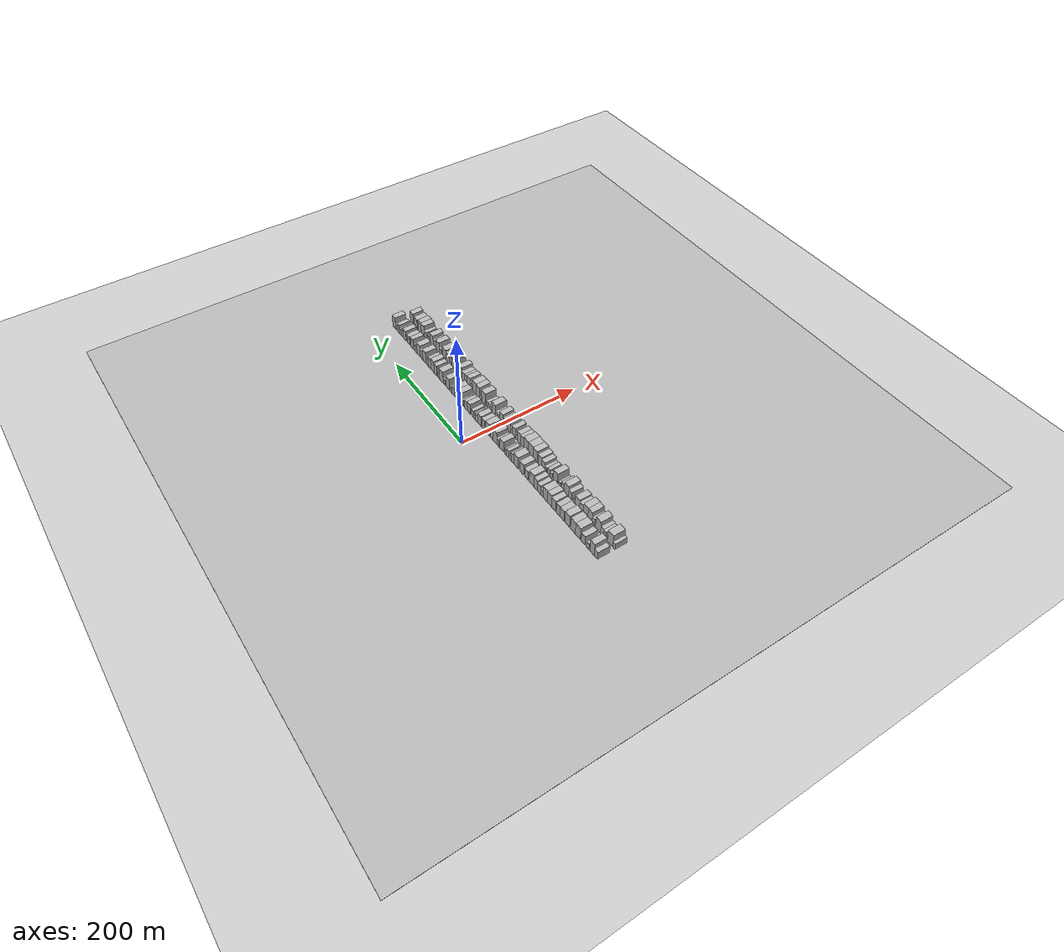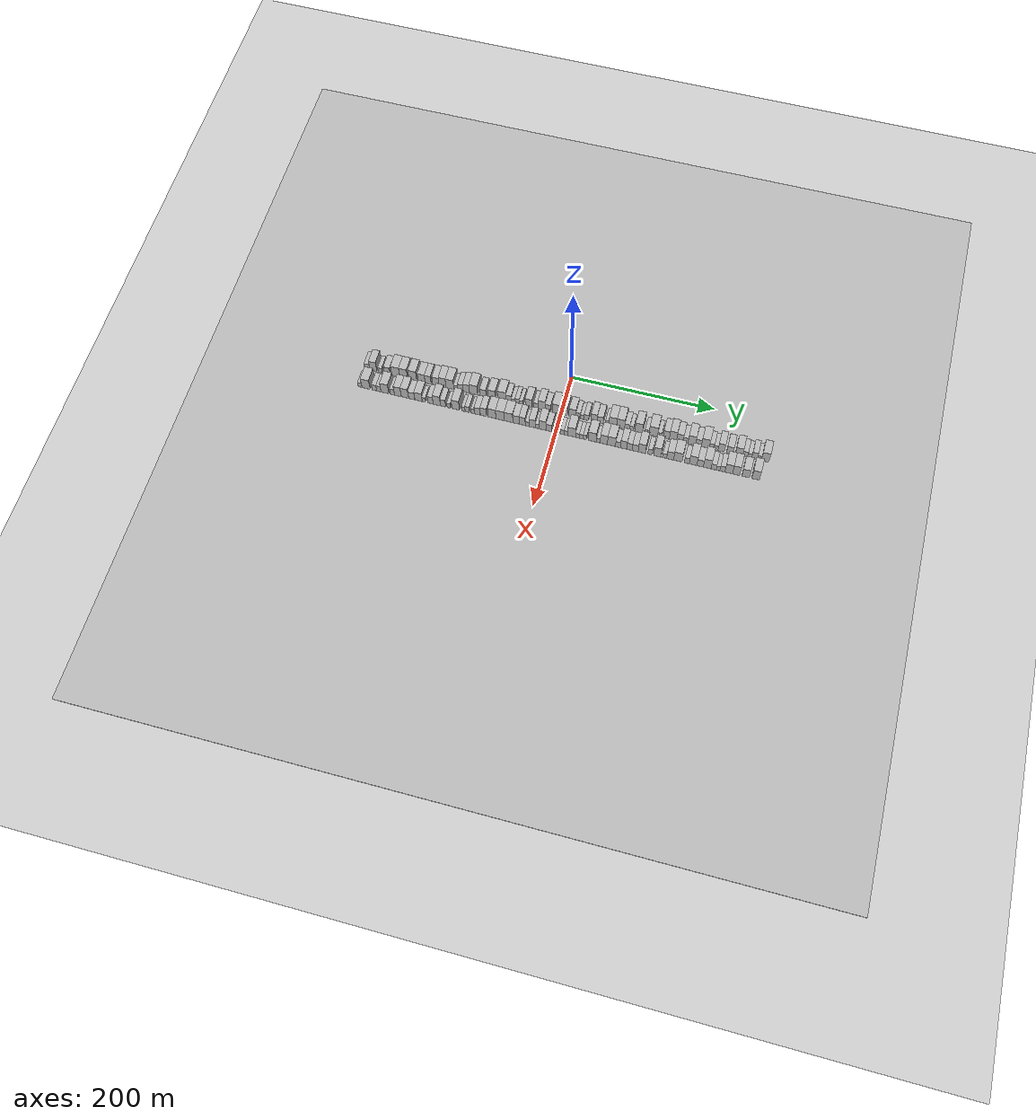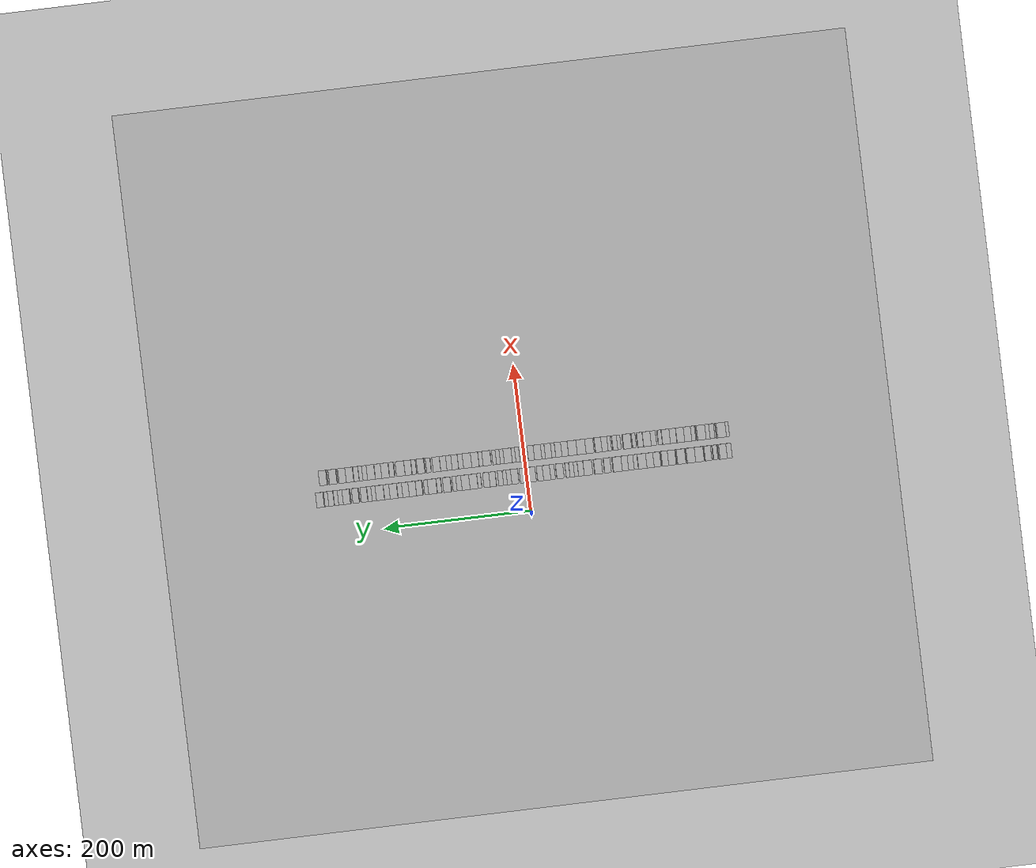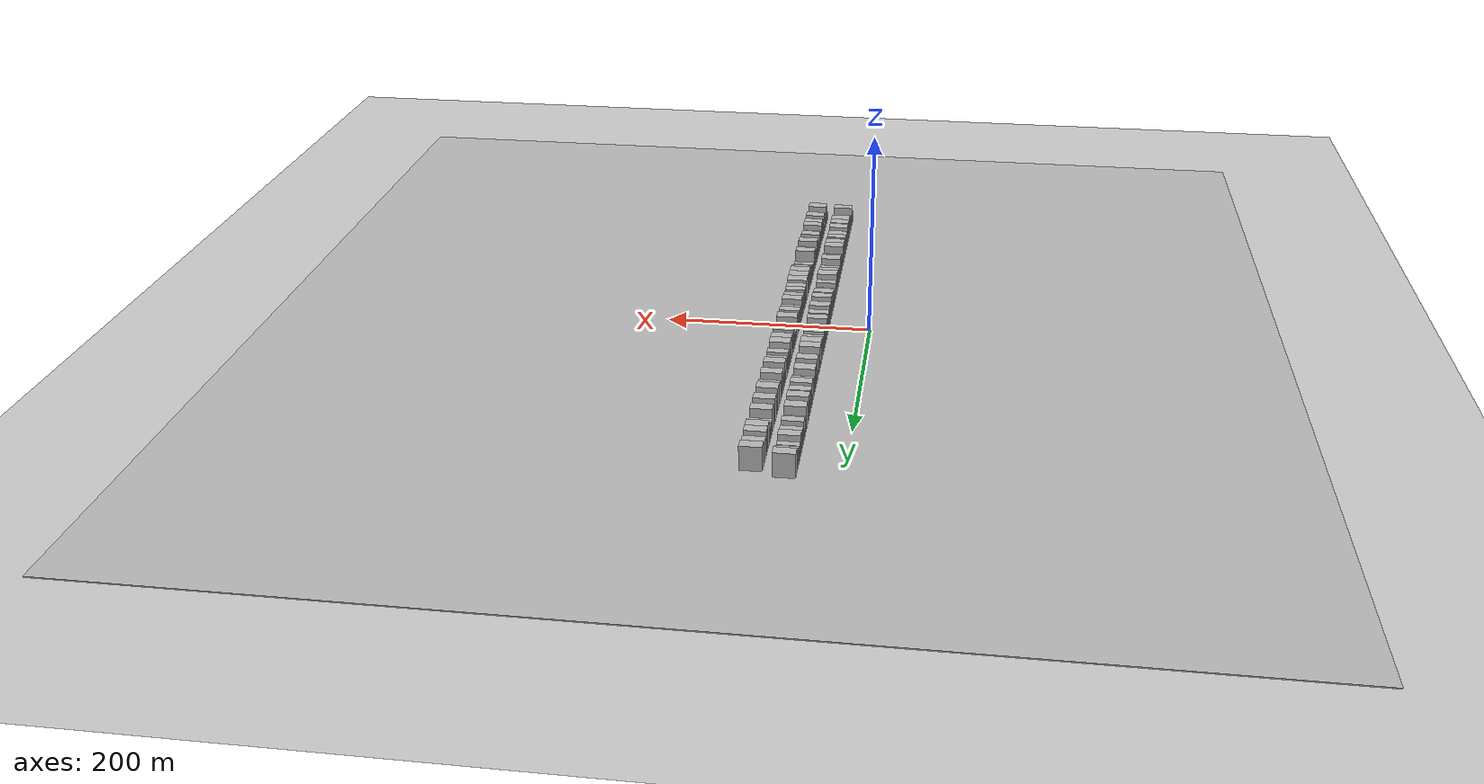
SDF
<?xml version="1.0" encoding="utf-8"?>

<sdf version="1.6">

   <world name="default">

      <gui fullscreen="0">

         <camera name="user_camera">

            <pose>-15 0 4.57585 0 0 0</pose>

            <view_controller>orbit</view_controller>

         </camera>

      </gui>

      <scene>

         <sky>

           <clouds>

             <speed>12</speed>

           </clouds>

         </sky>

         <ambient>0.4 0.4 0.4 1</ambient>

         <background>0.7 0.7 0.7 1</background>

         <shadows>1</shadows>

      </scene>

      <gravity>0 0 -9.8066</gravity>

      <magnetic_field>6e-06 2.3e-05 -4.2e-05</magnetic_field>

      <physics default="0" name="default_physics" type="ode">

         <ode>

            <solver>

               <type>quick</type>

               <iters>10</iters>

               <sor>1.0</sor>

               <use_dynamic_moi_rescaling>0</use_dynamic_moi_rescaling>

            </solver>

            <constraints>

               <cfm>0</cfm>

               <erp>0.2</erp>

               <contact_max_correcting_vel>100</contact_max_correcting_vel>

               <contact_surface_layer>0.001</contact_surface_layer>

            </constraints>

         </ode>

         <max_step_size>0.004</max_step_size>

         <real_time_factor>1</real_time_factor>

         <real_time_update_rate>250</real_time_update_rate>

      </physics>

      <light name="sun" type="directional">

         <cast_shadows>1</cast_shadows>

         <pose>0 0 10 0 0 0</pose>

         <diffuse>0.8 0.8 0.8 1</diffuse>

         <specular>0.2 0.2 0.2 1</specular>

         <attenuation>

            <range>1000</range>

            <constant>0.9</constant>

            <linear>0.01</linear>

            <quadratic>0.001</quadratic>

         </attenuation>

         <direction>-0.5 0.1 -0.9</direction>

      </light>

      <include>

         <name>ground_plane_1</name>

         <uri>model://HANNAS_ground_plane</uri>

         <pose>0 0 0  0 0 0</pose>

      </include>

      <include>

         <name>ground_plane_2</name>

         <uri>model://HANNAS_ground_plane</uri>

         <pose>100 0 0  0 0 0</pose>

      </include>

      <model name="building_1">

         <static>1</static>

         <pose frame="">50.0000 -274.2800 0 0.000000 0.000000 0.000000</pose>

         <link name="link">

            <pose frame="">0 0 7.50 0 0 0</pose>

            <collision name="collision">

               <geometry>

                  <box>

                     <size>20.0000 7.4400 15.0000</size>

                  </box>

               </geometry>

               <max_contacts>10</max_contacts>

               <surface>

                  <contact>

                     <ode/>

                  </contact>

                  <bounce/>

                  <friction>

                     <torsional>

                        <ode/>

                     </torsional>

                     <ode/>

                  </friction>

               </surface>

            </collision>

            <visual name="visual">

               <cast_shadows>0</cast_shadows>

               <geometry>

                  <box>

                     <size>20.0000 7.4400 15.0000</size>

                  </box>

               </geometry>

               <material>

                  <script>

                     <uri>model://HANNAS_wall/materials/scripts</uri>

                     <uri>model://HANNAS_wall/materials/textures</uri>

                     <name>vrc/HANNAS_wall</name>

                  </script>

               </material>

            </visual>

            <self_collide>0</self_collide>

            <enable_wind>0</enable_wind>

            <kinematic>0</kinematic>

         </link>

      </model>

      <model name="building_2">

         <static>1</static>

         <pose frame="">50.0000 -265.6306 0 0.000000 0.000000 0.000000</pose>

         <link name="link">

            <pose frame="">0 0 12.00 0 0 0</pose>

            <collision name="collision">

               <geometry>

                  <box>

                     <size>20.0000 9.8587 24.0000</size>

                  </box>

               </geometry>

               <max_contacts>10</max_contacts>

               <surface>

                  <contact>

                     <ode/>

                  </contact>

                  <bounce/>

                  <friction>

                     <torsional>

                        <ode/>

                     </torsional>

                     <ode/>

                  </friction>

               </surface>

            </collision>

            <visual name="visual">

               <cast_shadows>0</cast_shadows>

               <geometry>

                  <box>

                     <size>20.0000 9.8587 24.0000</size>

                  </box>

               </geometry>

               <material>

                  <script>

                     <uri>model://HANNAS_wall/materials/scripts</uri>

                     <uri>model://HANNAS_wall/materials/textures</uri>

                     <name>vrc/HANNAS_wall</name>

                  </script>

               </material>

            </visual>

            <self_collide>0</self_collide>

            <enable_wind>0</enable_wind>

            <kinematic>0</kinematic>

         </link>

      </model>

      <model name="building_3">

         <static>1</static>

         <pose frame="">50.0000 -255.8644 0 0.000000 0.000000 0.000000</pose>

         <link name="link">

            <pose frame="">0 0 6.00 0 0 0</pose>

            <collision name="collision">

               <geometry>

                  <box>

                     <size>20.0000 5.6739 12.0000</size>

                  </box>

               </geometry>

               <max_contacts>10</max_contacts>

               <surface>

                  <contact>

                     <ode/>

                  </contact>

                  <bounce/>

                  <friction>

                     <torsional>

                        <ode/>

                     </torsional>

                     <ode/>

                  </friction>

               </surface>

            </collision>

            <visual name="visual">

               <cast_shadows>0</cast_shadows>

               <geometry>

                  <box>

                     <size>20.0000 5.6739 12.0000</size>

                  </box>

               </geometry>

               <material>

                  <script>

                     <uri>model://HANNAS_wall/materials/scripts</uri>

                     <uri>model://HANNAS_wall/materials/textures</uri>

                     <name>vrc/HANNAS_wall</name>

                  </script>

               </material>

            </visual>

            <self_collide>0</self_collide>

            <enable_wind>0</enable_wind>

            <kinematic>0</kinematic>

         </link>

      </model>

      <model name="building_4">

         <static>1</static>

         <pose frame="">50.0000 -245.6716 0 0.000000 0.000000 0.000000</pose>

         <link name="link">

            <pose frame="">0 0 9.00 0 0 0</pose>

            <collision name="collision">

               <geometry>

                  <box>

                     <size>20.0000 8.7116 18.0000</size>

                  </box>

               </geometry>

               <max_contacts>10</max_contacts>

               <surface>

                  <contact>

                     <ode/>

                  </contact>

                  <bounce/>

                  <friction>

                     <torsional>

                        <ode/>

                     </torsional>

                     <ode/>

                  </friction>

               </surface>

            </collision>

            <visual name="visual">

               <cast_shadows>0</cast_shadows>

               <geometry>

                  <box>

                     <size>20.0000 8.7116 18.0000</size>

                  </box>

               </geometry>

               <material>

                  <script>

                     <uri>model://HANNAS_wall/materials/scripts</uri>

                     <uri>model://HANNAS_wall/materials/textures</uri>

                     <name>vrc/HANNAS_wall</name>

                  </script>

               </material>

            </visual>

            <self_collide>0</self_collide>

            <enable_wind>0</enable_wind>

            <kinematic>0</kinematic>

         </link>

      </model>

      <model name="building_5">

         <static>1</static>

         <pose frame="">50.0000 -233.5031 0 0.000000 0.000000 0.000000</pose>

         <link name="link">

            <pose frame="">0 0 12.00 0 0 0</pose>

            <collision name="collision">

               <geometry>

                  <box>

                     <size>20.0000 11.6254 24.0000</size>

                  </box>

               </geometry>

               <max_contacts>10</max_contacts>

               <surface>

                  <contact>

                     <ode/>

                  </contact>

                  <bounce/>

                  <friction>

                     <torsional>

                        <ode/>

                     </torsional>

                     <ode/>

                  </friction>

               </surface>

            </collision>

            <visual name="visual">

               <cast_shadows>0</cast_shadows>

               <geometry>

                  <box>

                     <size>20.0000 11.6254 24.0000</size>

                  </box>

               </geometry>

               <material>

                  <script>

                     <uri>model://HANNAS_wall/materials/scripts</uri>

                     <uri>model://HANNAS_wall/materials/textures</uri>

                     <name>vrc/HANNAS_wall</name>

                  </script>

               </material>

            </visual>

            <self_collide>0</self_collide>

            <enable_wind>0</enable_wind>

            <kinematic>0</kinematic>

         </link>

      </model>

      <model name="building_6">

         <static>1</static>

         <pose frame="">50.0000 -222.1084 0 0.000000 0.000000 0.000000</pose>

         <link name="link">

            <pose frame="">0 0 12.00 0 0 0</pose>

            <collision name="collision">

               <geometry>

                  <box>

                     <size>20.0000 11.1640 24.0000</size>

                  </box>

               </geometry>

               <max_contacts>10</max_contacts>

               <surface>

                  <contact>

                     <ode/>

                  </contact>

                  <bounce/>

                  <friction>

                     <torsional>

                        <ode/>

                     </torsional>

                     <ode/>

                  </friction>

               </surface>

            </collision>

            <visual name="visual">

               <cast_shadows>0</cast_shadows>

               <geometry>

                  <box>

                     <size>20.0000 11.1640 24.0000</size>

                  </box>

               </geometry>

               <material>

                  <script>

                     <uri>model://HANNAS_wall/materials/scripts</uri>

                     <uri>model://HANNAS_wall/materials/textures</uri>

                     <name>vrc/HANNAS_wall</name>

                  </script>

               </material>

            </visual>

            <self_collide>0</self_collide>

            <enable_wind>0</enable_wind>

            <kinematic>0</kinematic>

         </link>

      </model>

      <model name="building_7">

         <static>1</static>

         <pose frame="">50.0000 -208.9661 0 0.000000 0.000000 0.000000</pose>

         <link name="link">

            <pose frame="">0 0 12.00 0 0 0</pose>

            <collision name="collision">

               <geometry>

                  <box>

                     <size>20.0000 11.1205 24.0000</size>

                  </box>

               </geometry>

               <max_contacts>10</max_contacts>

               <surface>

                  <contact>

                     <ode/>

                  </contact>

                  <bounce/>

                  <friction>

                     <torsional>

                        <ode/>

                     </torsional>

                     <ode/>

                  </friction>

               </surface>

            </collision>

            <visual name="visual">

               <cast_shadows>0</cast_shadows>

               <geometry>

                  <box>

                     <size>20.0000 11.1205 24.0000</size>

                  </box>

               </geometry>

               <material>

                  <script>

                     <uri>model://HANNAS_wall/materials/scripts</uri>

                     <uri>model://HANNAS_wall/materials/textures</uri>

                     <name>vrc/HANNAS_wall</name>

                  </script>

               </material>

            </visual>

            <self_collide>0</self_collide>

            <enable_wind>0</enable_wind>

            <kinematic>0</kinematic>

         </link>

      </model>

      <model name="building_8">

         <static>1</static>

         <pose frame="">50.0000 -196.3599 0 0.000000 0.000000 0.000000</pose>

         <link name="link">

            <pose frame="">0 0 10.50 0 0 0</pose>

            <collision name="collision">

               <geometry>

                  <box>

                     <size>20.0000 10.0919 21.0000</size>

                  </box>

               </geometry>

               <max_contacts>10</max_contacts>

               <surface>

                  <contact>

                     <ode/>

                  </contact>

                  <bounce/>

                  <friction>

                     <torsional>

                        <ode/>

                     </torsional>

                     <ode/>

                  </friction>

               </surface>

            </collision>

            <visual name="visual">

               <cast_shadows>0</cast_shadows>

               <geometry>

                  <box>

                     <size>20.0000 10.0919 21.0000</size>

                  </box>

               </geometry>

               <material>

                  <script>

                     <uri>model://HANNAS_wall/materials/scripts</uri>

                     <uri>model://HANNAS_wall/materials/textures</uri>

                     <name>vrc/HANNAS_wall</name>

                  </script>

               </material>

            </visual>

            <self_collide>0</self_collide>

            <enable_wind>0</enable_wind>

            <kinematic>0</kinematic>

         </link>

      </model>

      <model name="building_9">

         <static>1</static>

         <pose frame="">50.0000 -187.0492 0 0.000000 0.000000 0.000000</pose>

         <link name="link">

            <pose frame="">0 0 10.50 0 0 0</pose>

            <collision name="collision">

               <geometry>

                  <box>

                     <size>20.0000 8.5296 21.0000</size>

                  </box>

               </geometry>

               <max_contacts>10</max_contacts>

               <surface>

                  <contact>

                     <ode/>

                  </contact>

                  <bounce/>

                  <friction>

                     <torsional>

                        <ode/>

                     </torsional>

                     <ode/>

                  </friction>

               </surface>

            </collision>

            <visual name="visual">

               <cast_shadows>0</cast_shadows>

               <geometry>

                  <box>

                     <size>20.0000 8.5296 21.0000</size>

                  </box>

               </geometry>

               <material>

                  <script>

                     <uri>model://HANNAS_wall/materials/scripts</uri>

                     <uri>model://HANNAS_wall/materials/textures</uri>

                     <name>vrc/HANNAS_wall</name>

                  </script>

               </material>

            </visual>

            <self_collide>0</self_collide>

            <enable_wind>0</enable_wind>

            <kinematic>0</kinematic>

         </link>

      </model>

      <model name="building_10">

         <static>1</static>

         <pose frame="">50.0000 -176.1202 0 0.000000 0.000000 0.000000</pose>

         <link name="link">

            <pose frame="">0 0 10.50 0 0 0</pose>

            <collision name="collision">

               <geometry>

                  <box>

                     <size>20.0000 9.3284 21.0000</size>

                  </box>

               </geometry>

               <max_contacts>10</max_contacts>

               <surface>

                  <contact>

                     <ode/>

                  </contact>

                  <bounce/>

                  <friction>

                     <torsional>

                        <ode/>

                     </torsional>

                     <ode/>

                  </friction>

               </surface>

            </collision>

            <visual name="visual">

               <cast_shadows>0</cast_shadows>

               <geometry>

                  <box>

                     <size>20.0000 9.3284 21.0000</size>

                  </box>

               </geometry>

               <material>

                  <script>

                     <uri>model://HANNAS_wall/materials/scripts</uri>

                     <uri>model://HANNAS_wall/materials/textures</uri>

                     <name>vrc/HANNAS_wall</name>

                  </script>

               </material>

            </visual>

            <self_collide>0</self_collide>

            <enable_wind>0</enable_wind>

            <kinematic>0</kinematic>

         </link>

      </model>

      <model name="building_11">

         <static>1</static>

         <pose frame="">50.0000 -166.5818 0 0.000000 0.000000 0.000000</pose>

         <link name="link">

            <pose frame="">0 0 12.00 0 0 0</pose>

            <collision name="collision">

               <geometry>

                  <box>

                     <size>20.0000 9.7484 24.0000</size>

                  </box>

               </geometry>

               <max_contacts>10</max_contacts>

               <surface>

                  <contact>

                     <ode/>

                  </contact>

                  <bounce/>

                  <friction>

                     <torsional>

                        <ode/>

                     </torsional>

                     <ode/>

                  </friction>

               </surface>

            </collision>

            <visual name="visual">

               <cast_shadows>0</cast_shadows>

               <geometry>

                  <box>

                     <size>20.0000 9.7484 24.0000</size>

                  </box>

               </geometry>

               <material>

                  <script>

                     <uri>model://HANNAS_wall/materials/scripts</uri>

                     <uri>model://HANNAS_wall/materials/textures</uri>

                     <name>vrc/HANNAS_wall</name>

                  </script>

               </material>

            </visual>

            <self_collide>0</self_collide>

            <enable_wind>0</enable_wind>

            <kinematic>0</kinematic>

         </link>

      </model>

      <model name="building_12">

         <static>1</static>

         <pose frame="">50.0000 -156.0734 0 0.000000 0.000000 0.000000</pose>

         <link name="link">

            <pose frame="">0 0 12.00 0 0 0</pose>

            <collision name="collision">

               <geometry>

                  <box>

                     <size>20.0000 11.2684 24.0000</size>

                  </box>

               </geometry>

               <max_contacts>10</max_contacts>

               <surface>

                  <contact>

                     <ode/>

                  </contact>

                  <bounce/>

                  <friction>

                     <torsional>

                        <ode/>

                     </torsional>

                     <ode/>

                  </friction>

               </surface>

            </collision>

            <visual name="visual">

               <cast_shadows>0</cast_shadows>

               <geometry>

                  <box>

                     <size>20.0000 11.2684 24.0000</size>

                  </box>

               </geometry>

               <material>

                  <script>

                     <uri>model://HANNAS_wall/materials/scripts</uri>

                     <uri>model://HANNAS_wall/materials/textures</uri>

                     <name>vrc/HANNAS_wall</name>

                  </script>

               </material>

            </visual>

            <self_collide>0</self_collide>

            <enable_wind>0</enable_wind>

            <kinematic>0</kinematic>

         </link>

      </model>

      <model name="building_13">

         <static>1</static>

         <pose frame="">50.0000 -147.5744 0 0.000000 0.000000 0.000000</pose>

         <link name="link">

            <pose frame="">0 0 6.00 0 0 0</pose>

            <collision name="collision">

               <geometry>

                  <box>

                     <size>20.0000 5.7296 12.0000</size>

                  </box>

               </geometry>

               <max_contacts>10</max_contacts>

               <surface>

                  <contact>

                     <ode/>

                  </contact>

                  <bounce/>

                  <friction>

                     <torsional>

                        <ode/>

                     </torsional>

                     <ode/>

                  </friction>

               </surface>

            </collision>

            <visual name="visual">

               <cast_shadows>0</cast_shadows>

               <geometry>

                  <box>

                     <size>20.0000 5.7296 12.0000</size>

                  </box>

               </geometry>

               <material>

                  <script>

                     <uri>model://HANNAS_wall/materials/scripts</uri>

                     <uri>model://HANNAS_wall/materials/textures</uri>

                     <name>vrc/HANNAS_wall</name>

                  </script>

               </material>

            </visual>

            <self_collide>0</self_collide>

            <enable_wind>0</enable_wind>

            <kinematic>0</kinematic>

         </link>

      </model>

      <model name="building_14">

         <static>1</static>

         <pose frame="">50.0000 -140.8800 0 0.000000 0.000000 0.000000</pose>

         <link name="link">

            <pose frame="">0 0 9.00 0 0 0</pose>

            <collision name="collision">

               <geometry>

                  <box>

                     <size>20.0000 7.6592 18.0000</size>

                  </box>

               </geometry>

               <max_contacts>10</max_contacts>

               <surface>

                  <contact>

                     <ode/>

                  </contact>

                  <bounce/>

                  <friction>

                     <torsional>

                        <ode/>

                     </torsional>

                     <ode/>

                  </friction>

               </surface>

            </collision>

            <visual name="visual">

               <cast_shadows>0</cast_shadows>

               <geometry>

                  <box>

                     <size>20.0000 7.6592 18.0000</size>

                  </box>

               </geometry>

               <material>

                  <script>

                     <uri>model://HANNAS_wall/materials/scripts</uri>

                     <uri>model://HANNAS_wall/materials/textures</uri>

                     <name>vrc/HANNAS_wall</name>

                  </script>

               </material>

            </visual>

            <self_collide>0</self_collide>

            <enable_wind>0</enable_wind>

            <kinematic>0</kinematic>

         </link>

      </model>

      <model name="building_15">

         <static>1</static>

         <pose frame="">50.0000 -132.6836 0 0.000000 0.000000 0.000000</pose>

         <link name="link">

            <pose frame="">0 0 10.50 0 0 0</pose>

            <collision name="collision">

               <geometry>

                  <box>

                     <size>20.0000 8.7337 21.0000</size>

                  </box>

               </geometry>

               <max_contacts>10</max_contacts>

               <surface>

                  <contact>

                     <ode/>

                  </contact>

                  <bounce/>

                  <friction>

                     <torsional>

                        <ode/>

                     </torsional>

                     <ode/>

                  </friction>

               </surface>

            </collision>

            <visual name="visual">

               <cast_shadows>0</cast_shadows>

               <geometry>

                  <box>

                     <size>20.0000 8.7337 21.0000</size>

                  </box>

               </geometry>

               <material>

                  <script>

                     <uri>model://HANNAS_wall/materials/scripts</uri>

                     <uri>model://HANNAS_wall/materials/textures</uri>

                     <name>vrc/HANNAS_wall</name>

                  </script>

               </material>

            </visual>

            <self_collide>0</self_collide>

            <enable_wind>0</enable_wind>

            <kinematic>0</kinematic>

         </link>

      </model>

      <model name="building_16">

         <static>1</static>

         <pose frame="">50.0000 -122.4694 0 0.000000 0.000000 0.000000</pose>

         <link name="link">

            <pose frame="">0 0 12.00 0 0 0</pose>

            <collision name="collision">

               <geometry>

                  <box>

                     <size>20.0000 11.6947 24.0000</size>

                  </box>

               </geometry>

               <max_contacts>10</max_contacts>

               <surface>

                  <contact>

                     <ode/>

                  </contact>

                  <bounce/>

                  <friction>

                     <torsional>

                        <ode/>

                     </torsional>

                     <ode/>

                  </friction>

               </surface>

            </collision>

            <visual name="visual">

               <cast_shadows>0</cast_shadows>

               <geometry>

                  <box>

                     <size>20.0000 11.6947 24.0000</size>

                  </box>

               </geometry>

               <material>

                  <script>

                     <uri>model://HANNAS_wall/materials/scripts</uri>

                     <uri>model://HANNAS_wall/materials/textures</uri>

                     <name>vrc/HANNAS_wall</name>

                  </script>

               </material>

            </visual>

            <self_collide>0</self_collide>

            <enable_wind>0</enable_wind>

            <kinematic>0</kinematic>

         </link>

      </model>

      <model name="building_17">

         <static>1</static>

         <pose frame="">50.0000 -109.2025 0 0.000000 0.000000 0.000000</pose>

         <link name="link">

            <pose frame="">0 0 9.00 0 0 0</pose>

            <collision name="collision">

               <geometry>

                  <box>

                     <size>20.0000 8.8392 18.0000</size>

                  </box>

               </geometry>

               <max_contacts>10</max_contacts>

               <surface>

                  <contact>

                     <ode/>

                  </contact>

                  <bounce/>

                  <friction>

                     <torsional>

                        <ode/>

                     </torsional>

                     <ode/>

                  </friction>

               </surface>

            </collision>

            <visual name="visual">

               <cast_shadows>0</cast_shadows>

               <geometry>

                  <box>

                     <size>20.0000 8.8392 18.0000</size>

                  </box>

               </geometry>

               <material>

                  <script>

                     <uri>model://HANNAS_wall/materials/scripts</uri>

                     <uri>model://HANNAS_wall/materials/textures</uri>

                     <name>vrc/HANNAS_wall</name>

                  </script>

               </material>

            </visual>

            <self_collide>0</self_collide>

            <enable_wind>0</enable_wind>

            <kinematic>0</kinematic>

         </link>

      </model>

      <model name="building_18">

         <static>1</static>

         <pose frame="">50.0000 -96.5926 0 0.000000 0.000000 0.000000</pose>

         <link name="link">

            <pose frame="">0 0 10.50 0 0 0</pose>

            <collision name="collision">

               <geometry>

                  <box>

                     <size>20.0000 10.3805 21.0000</size>

                  </box>

               </geometry>

               <max_contacts>10</max_contacts>

               <surface>

                  <contact>

                     <ode/>

                  </contact>

                  <bounce/>

                  <friction>

                     <torsional>

                        <ode/>

                     </torsional>

                     <ode/>

                  </friction>

               </surface>

            </collision>

            <visual name="visual">

               <cast_shadows>0</cast_shadows>

               <geometry>

                  <box>

                     <size>20.0000 10.3805 21.0000</size>

                  </box>

               </geometry>

               <material>

                  <script>

                     <uri>model://HANNAS_wall/materials/scripts</uri>

                     <uri>model://HANNAS_wall/materials/textures</uri>

                     <name>vrc/HANNAS_wall</name>

                  </script>

               </material>

            </visual>

            <self_collide>0</self_collide>

            <enable_wind>0</enable_wind>

            <kinematic>0</kinematic>

         </link>

      </model>

      <model name="building_19">

         <static>1</static>

         <pose frame="">50.0000 -82.6011 0 0.000000 0.000000 0.000000</pose>

         <link name="link">

            <pose frame="">0 0 12.00 0 0 0</pose>

            <collision name="collision">

               <geometry>

                  <box>

                     <size>20.0000 11.6026 24.0000</size>

                  </box>

               </geometry>

               <max_contacts>10</max_contacts>

               <surface>

                  <contact>

                     <ode/>

                  </contact>

                  <bounce/>

                  <friction>

                     <torsional>

                        <ode/>

                     </torsional>

                     <ode/>

                  </friction>

               </surface>

            </collision>

            <visual name="visual">

               <cast_shadows>0</cast_shadows>

               <geometry>

                  <box>

                     <size>20.0000 11.6026 24.0000</size>

                  </box>

               </geometry>

               <material>

                  <script>

                     <uri>model://HANNAS_wall/materials/scripts</uri>

                     <uri>model://HANNAS_wall/materials/textures</uri>

                     <name>vrc/HANNAS_wall</name>

                  </script>

               </material>

            </visual>

            <self_collide>0</self_collide>

            <enable_wind>0</enable_wind>

            <kinematic>0</kinematic>

         </link>

      </model>

      <model name="building_20">

         <static>1</static>

         <pose frame="">50.0000 -72.9751 0 0.000000 0.000000 0.000000</pose>

         <link name="link">

            <pose frame="">0 0 9.00 0 0 0</pose>

            <collision name="collision">

               <geometry>

                  <box>

                     <size>20.0000 7.6494 18.0000</size>

                  </box>

               </geometry>

               <max_contacts>10</max_contacts>

               <surface>

                  <contact>

                     <ode/>

                  </contact>

                  <bounce/>

                  <friction>

                     <torsional>

                        <ode/>

                     </torsional>

                     <ode/>

                  </friction>

               </surface>

            </collision>

            <visual name="visual">

               <cast_shadows>0</cast_shadows>

               <geometry>

                  <box>

                     <size>20.0000 7.6494 18.0000</size>

                  </box>

               </geometry>

               <material>

                  <script>

                     <uri>model://HANNAS_wall/materials/scripts</uri>

                     <uri>model://HANNAS_wall/materials/textures</uri>

                     <name>vrc/HANNAS_wall</name>

                  </script>

               </material>

            </visual>

            <self_collide>0</self_collide>

            <enable_wind>0</enable_wind>

            <kinematic>0</kinematic>

         </link>

      </model>

      <model name="building_21">

         <static>1</static>

         <pose frame="">50.0000 -66.4450 0 0.000000 0.000000 0.000000</pose>

         <link name="link">

            <pose frame="">0 0 6.00 0 0 0</pose>

            <collision name="collision">

               <geometry>

                  <box>

                     <size>20.0000 5.4107 12.0000</size>

                  </box>

               </geometry>

               <max_contacts>10</max_contacts>

               <surface>

                  <contact>

                     <ode/>

                  </contact>

                  <bounce/>

                  <friction>

                     <torsional>

                        <ode/>

                     </torsional>

                     <ode/>

                  </friction>

               </surface>

            </collision>

            <visual name="visual">

               <cast_shadows>0</cast_shadows>

               <geometry>

                  <box>

                     <size>20.0000 5.4107 12.0000</size>

                  </box>

               </geometry>

               <material>

                  <script>

                     <uri>model://HANNAS_wall/materials/scripts</uri>

                     <uri>model://HANNAS_wall/materials/textures</uri>

                     <name>vrc/HANNAS_wall</name>

                  </script>

               </material>

            </visual>

            <self_collide>0</self_collide>

            <enable_wind>0</enable_wind>

            <kinematic>0</kinematic>

         </link>

      </model>

      <model name="building_22">

         <static>1</static>

         <pose frame="">50.0000 -60.7023 0 0.000000 0.000000 0.000000</pose>

         <link name="link">

            <pose frame="">0 0 7.50 0 0 0</pose>

            <collision name="collision">

               <geometry>

                  <box>

                     <size>20.0000 6.0748 15.0000</size>

                  </box>

               </geometry>

               <max_contacts>10</max_contacts>

               <surface>

                  <contact>

                     <ode/>

                  </contact>

                  <bounce/>

                  <friction>

                     <torsional>

                        <ode/>

                     </torsional>

                     <ode/>

                  </friction>

               </surface>

            </collision>

            <visual name="visual">

               <cast_shadows>0</cast_shadows>

               <geometry>

                  <box>

                     <size>20.0000 6.0748 15.0000</size>

                  </box>

               </geometry>

               <material>

                  <script>

                     <uri>model://HANNAS_wall/materials/scripts</uri>

                     <uri>model://HANNAS_wall/materials/textures</uri>

                     <name>vrc/HANNAS_wall</name>

                  </script>

               </material>

            </visual>

            <self_collide>0</self_collide>

            <enable_wind>0</enable_wind>

            <kinematic>0</kinematic>

         </link>

      </model>

      <model name="building_23">

         <static>1</static>

         <pose frame="">50.0000 -55.1028 0 0.000000 0.000000 0.000000</pose>

         <link name="link">

            <pose frame="">0 0 6.00 0 0 0</pose>

            <collision name="collision">

               <geometry>

                  <box>

                     <size>20.0000 5.1241 12.0000</size>

                  </box>

               </geometry>

               <max_contacts>10</max_contacts>

               <surface>

                  <contact>

                     <ode/>

                  </contact>

                  <bounce/>

                  <friction>

                     <torsional>

                        <ode/>

                     </torsional>

                     <ode/>

                  </friction>

               </surface>

            </collision>

            <visual name="visual">

               <cast_shadows>0</cast_shadows>

               <geometry>

                  <box>

                     <size>20.0000 5.1241 12.0000</size>

                  </box>

               </geometry>

               <material>

                  <script>

                     <uri>model://HANNAS_wall/materials/scripts</uri>

                     <uri>model://HANNAS_wall/materials/textures</uri>

                     <name>vrc/HANNAS_wall</name>

                  </script>

               </material>

            </visual>

            <self_collide>0</self_collide>

            <enable_wind>0</enable_wind>

            <kinematic>0</kinematic>

         </link>

      </model>

      <model name="building_24">

         <static>1</static>

         <pose frame="">50.0000 -44.6592 0 0.000000 0.000000 0.000000</pose>

         <link name="link">

            <pose frame="">0 0 10.50 0 0 0</pose>

            <collision name="collision">

               <geometry>

                  <box>

                     <size>20.0000 9.7632 21.0000</size>

                  </box>

               </geometry>

               <max_contacts>10</max_contacts>

               <surface>

                  <contact>

                     <ode/>

                  </contact>

                  <bounce/>

                  <friction>

                     <torsional>

                        <ode/>

                     </torsional>

                     <ode/>

                  </friction>

               </surface>

            </collision>

            <visual name="visual">

               <cast_shadows>0</cast_shadows>

               <geometry>

                  <box>

                     <size>20.0000 9.7632 21.0000</size>

                  </box>

               </geometry>

               <material>

                  <script>

                     <uri>model://HANNAS_wall/materials/scripts</uri>

                     <uri>model://HANNAS_wall/materials/textures</uri>

                     <name>vrc/HANNAS_wall</name>

                  </script>

               </material>

            </visual>

            <self_collide>0</self_collide>

            <enable_wind>0</enable_wind>

            <kinematic>0</kinematic>

         </link>

      </model>

      <model name="building_25">

         <static>1</static>

         <pose frame="">50.0000 -34.6333 0 0.000000 0.000000 0.000000</pose>

         <link name="link">

            <pose frame="">0 0 7.50 0 0 0</pose>

            <collision name="collision">

               <geometry>

                  <box>

                     <size>20.0000 6.2885 15.0000</size>

                  </box>

               </geometry>

               <max_contacts>10</max_contacts>

               <surface>

                  <contact>

                     <ode/>

                  </contact>

                  <bounce/>

                  <friction>

                     <torsional>

                        <ode/>

                     </torsional>

                     <ode/>

                  </friction>

               </surface>

            </collision>

            <visual name="visual">

               <cast_shadows>0</cast_shadows>

               <geometry>

                  <box>

                     <size>20.0000 6.2885 15.0000</size>

                  </box>

               </geometry>

               <material>

                  <script>

                     <uri>model://HANNAS_wall/materials/scripts</uri>

                     <uri>model://HANNAS_wall/materials/textures</uri>

                     <name>vrc/HANNAS_wall</name>

                  </script>

               </material>

            </visual>

            <self_collide>0</self_collide>

            <enable_wind>0</enable_wind>

            <kinematic>0</kinematic>

         </link>

      </model>

      <model name="building_26">

         <static>1</static>

         <pose frame="">50.0000 -26.6093 0 0.000000 0.000000 0.000000</pose>

         <link name="link">

            <pose frame="">0 0 12.00 0 0 0</pose>

            <collision name="collision">

               <geometry>

                  <box>

                     <size>20.0000 9.7597 24.0000</size>

                  </box>

               </geometry>

               <max_contacts>10</max_contacts>

               <surface>

                  <contact>

                     <ode/>

                  </contact>

                  <bounce/>

                  <friction>

                     <torsional>

                        <ode/>

                     </torsional>

                     <ode/>

                  </friction>

               </surface>

            </collision>

            <visual name="visual">

               <cast_shadows>0</cast_shadows>

               <geometry>

                  <box>

                     <size>20.0000 9.7597 24.0000</size>

                  </box>

               </geometry>

               <material>

                  <script>

                     <uri>model://HANNAS_wall/materials/scripts</uri>

                     <uri>model://HANNAS_wall/materials/textures</uri>

                     <name>vrc/HANNAS_wall</name>

                  </script>

               </material>

            </visual>

            <self_collide>0</self_collide>

            <enable_wind>0</enable_wind>

            <kinematic>0</kinematic>

         </link>

      </model>

      <model name="building_27">

         <static>1</static>

         <pose frame="">50.0000 -17.7537 0 0.000000 0.000000 0.000000</pose>

         <link name="link">

            <pose frame="">0 0 9.00 0 0 0</pose>

            <collision name="collision">

               <geometry>

                  <box>

                     <size>20.0000 7.9515 18.0000</size>

                  </box>

               </geometry>

               <max_contacts>10</max_contacts>

               <surface>

                  <contact>

                     <ode/>

                  </contact>

                  <bounce/>

                  <friction>

                     <torsional>

                        <ode/>

                     </torsional>

                     <ode/>

                  </friction>

               </surface>

            </collision>

            <visual name="visual">

               <cast_shadows>0</cast_shadows>

               <geometry>

                  <box>

                     <size>20.0000 7.9515 18.0000</size>

                  </box>

               </geometry>

               <material>

                  <script>

                     <uri>model://HANNAS_wall/materials/scripts</uri>

                     <uri>model://HANNAS_wall/materials/textures</uri>

                     <name>vrc/HANNAS_wall</name>

                  </script>

               </material>

            </visual>

            <self_collide>0</self_collide>

            <enable_wind>0</enable_wind>

            <kinematic>0</kinematic>

         </link>

      </model>

      <model name="building_28">

         <static>1</static>

         <pose frame="">50.0000 -6.4030 0 0.000000 0.000000 0.000000</pose>

         <link name="link">

            <pose frame="">0 0 12.00 0 0 0</pose>

            <collision name="collision">

               <geometry>

                  <box>

                     <size>20.0000 10.7500 24.0000</size>

                  </box>

               </geometry>

               <max_contacts>10</max_contacts>

               <surface>

                  <contact>

                     <ode/>

                  </contact>

                  <bounce/>

                  <friction>

                     <torsional>

                        <ode/>

                     </torsional>

                     <ode/>

                  </friction>

               </surface>

            </collision>

            <visual name="visual">

               <cast_shadows>0</cast_shadows>

               <geometry>

                  <box>

                     <size>20.0000 10.7500 24.0000</size>

                  </box>

               </geometry>

               <material>

                  <script>

                     <uri>model://HANNAS_wall/materials/scripts</uri>

                     <uri>model://HANNAS_wall/materials/textures</uri>

                     <name>vrc/HANNAS_wall</name>

                  </script>

               </material>

            </visual>

            <self_collide>0</self_collide>

            <enable_wind>0</enable_wind>

            <kinematic>0</kinematic>

         </link>

      </model>

      <model name="building_29">

         <static>1</static>

         <pose frame="">50.0000 5.3258 0 0.000000 0.000000 0.000000</pose>

         <link name="link">

            <pose frame="">0 0 10.50 0 0 0</pose>

            <collision name="collision">

               <geometry>

                  <box>

                     <size>20.0000 8.7075 21.0000</size>

                  </box>

               </geometry>

               <max_contacts>10</max_contacts>

               <surface>

                  <contact>

                     <ode/>

                  </contact>

                  <bounce/>

                  <friction>

                     <torsional>

                        <ode/>

                     </torsional>

                     <ode/>

                  </friction>

               </surface>

            </collision>

            <visual name="visual">

               <cast_shadows>0</cast_shadows>

               <geometry>

                  <box>

                     <size>20.0000 8.7075 21.0000</size>

                  </box>

               </geometry>

               <material>

                  <script>

                     <uri>model://HANNAS_wall/materials/scripts</uri>

                     <uri>model://HANNAS_wall/materials/textures</uri>

                     <name>vrc/HANNAS_wall</name>

                  </script>

               </material>

            </visual>

            <self_collide>0</self_collide>

            <enable_wind>0</enable_wind>

            <kinematic>0</kinematic>

         </link>

      </model>

      <model name="building_30">

         <static>1</static>

         <pose frame="">50.0000 16.5006 0 0.000000 0.000000 0.000000</pose>

         <link name="link">

            <pose frame="">0 0 10.50 0 0 0</pose>

            <collision name="collision">

               <geometry>

                  <box>

                     <size>20.0000 9.6423 21.0000</size>

                  </box>

               </geometry>

               <max_contacts>10</max_contacts>

               <surface>

                  <contact>

                     <ode/>

                  </contact>

                  <bounce/>

                  <friction>

                     <torsional>

                        <ode/>

                     </torsional>

                     <ode/>

                  </friction>

               </surface>

            </collision>

            <visual name="visual">

               <cast_shadows>0</cast_shadows>

               <geometry>

                  <box>

                     <size>20.0000 9.6423 21.0000</size>

                  </box>

               </geometry>

               <material>

                  <script>

                     <uri>model://HANNAS_wall/materials/scripts</uri>

                     <uri>model://HANNAS_wall/materials/textures</uri>

                     <name>vrc/HANNAS_wall</name>

                  </script>

               </material>

            </visual>

            <self_collide>0</self_collide>

            <enable_wind>0</enable_wind>

            <kinematic>0</kinematic>

         </link>

      </model>

      <model name="building_31">

         <static>1</static>

         <pose frame="">50.0000 24.4151 0 0.000000 0.000000 0.000000</pose>

         <link name="link">

            <pose frame="">0 0 7.50 0 0 0</pose>

            <collision name="collision">

               <geometry>

                  <box>

                     <size>20.0000 6.1867 15.0000</size>

                  </box>

               </geometry>

               <max_contacts>10</max_contacts>

               <surface>

                  <contact>

                     <ode/>

                  </contact>

                  <bounce/>

                  <friction>

                     <torsional>

                        <ode/>

                     </torsional>

                     <ode/>

                  </friction>

               </surface>

            </collision>

            <visual name="visual">

               <cast_shadows>0</cast_shadows>

               <geometry>

                  <box>

                     <size>20.0000 6.1867 15.0000</size>

                  </box>

               </geometry>

               <material>

                  <script>

                     <uri>model://HANNAS_wall/materials/scripts</uri>

                     <uri>model://HANNAS_wall/materials/textures</uri>

                     <name>vrc/HANNAS_wall</name>

                  </script>

               </material>

            </visual>

            <self_collide>0</self_collide>

            <enable_wind>0</enable_wind>

            <kinematic>0</kinematic>

         </link>

      </model>

      <model name="building_32">

         <static>1</static>

         <pose frame="">50.0000 30.0523 0 0.000000 0.000000 0.000000</pose>

         <link name="link">

            <pose frame="">0 0 6.00 0 0 0</pose>

            <collision name="collision">

               <geometry>

                  <box>

                     <size>20.0000 5.0875 12.0000</size>

                  </box>

               </geometry>

               <max_contacts>10</max_contacts>

               <surface>

                  <contact>

                     <ode/>

                  </contact>

                  <bounce/>

                  <friction>

                     <torsional>

                        <ode/>

                     </torsional>

                     <ode/>

                  </friction>

               </surface>

            </collision>

            <visual name="visual">

               <cast_shadows>0</cast_shadows>

               <geometry>

                  <box>

                     <size>20.0000 5.0875 12.0000</size>

                  </box>

               </geometry>

               <material>

                  <script>

                     <uri>model://HANNAS_wall/materials/scripts</uri>

                     <uri>model://HANNAS_wall/materials/textures</uri>

                     <name>vrc/HANNAS_wall</name>

                  </script>

               </material>

            </visual>

            <self_collide>0</self_collide>

            <enable_wind>0</enable_wind>

            <kinematic>0</kinematic>

         </link>

      </model>

      <model name="building_33">

         <static>1</static>

         <pose frame="">50.0000 35.8845 0 0.000000 0.000000 0.000000</pose>

         <link name="link">

            <pose frame="">0 0 7.50 0 0 0</pose>

            <collision name="collision">

               <geometry>

                  <box>

                     <size>20.0000 6.5770 15.0000</size>

                  </box>

               </geometry>

               <max_contacts>10</max_contacts>

               <surface>

                  <contact>

                     <ode/>

                  </contact>

                  <bounce/>

                  <friction>

                     <torsional>

                        <ode/>

                     </torsional>

                     <ode/>

                  </friction>

               </surface>

            </collision>

            <visual name="visual">

               <cast_shadows>0</cast_shadows>

               <geometry>

                  <box>

                     <size>20.0000 6.5770 15.0000</size>

                  </box>

               </geometry>

               <material>

                  <script>

                     <uri>model://HANNAS_wall/materials/scripts</uri>

                     <uri>model://HANNAS_wall/materials/textures</uri>

                     <name>vrc/HANNAS_wall</name>

                  </script>

               </material>

            </visual>

            <self_collide>0</self_collide>

            <enable_wind>0</enable_wind>

            <kinematic>0</kinematic>

         </link>

      </model>

      <model name="building_34">

         <static>1</static>

         <pose frame="">50.0000 46.4833 0 0.000000 0.000000 0.000000</pose>

         <link name="link">

            <pose frame="">0 0 10.50 0 0 0</pose>

            <collision name="collision">

               <geometry>

                  <box>

                     <size>20.0000 8.6205 21.0000</size>

                  </box>

               </geometry>

               <max_contacts>10</max_contacts>

               <surface>

                  <contact>

                     <ode/>

                  </contact>

                  <bounce/>

                  <friction>

                     <torsional>

                        <ode/>

                     </torsional>

                     <ode/>

                  </friction>

               </surface>

            </collision>

            <visual name="visual">

               <cast_shadows>0</cast_shadows>

               <geometry>

                  <box>

                     <size>20.0000 8.6205 21.0000</size>

                  </box>

               </geometry>

               <material>

                  <script>

                     <uri>model://HANNAS_wall/materials/scripts</uri>

                     <uri>model://HANNAS_wall/materials/textures</uri>

                     <name>vrc/HANNAS_wall</name>

                  </script>

               </material>

            </visual>

            <self_collide>0</self_collide>

            <enable_wind>0</enable_wind>

            <kinematic>0</kinematic>

         </link>

      </model>

      <model name="building_35">

         <static>1</static>

         <pose frame="">50.0000 55.0244 0 0.000000 0.000000 0.000000</pose>

         <link name="link">

            <pose frame="">0 0 9.00 0 0 0</pose>

            <collision name="collision">

               <geometry>

                  <box>

                     <size>20.0000 8.4618 18.0000</size>

                  </box>

               </geometry>

               <max_contacts>10</max_contacts>

               <surface>

                  <contact>

                     <ode/>

                  </contact>

                  <bounce/>

                  <friction>

                     <torsional>

                        <ode/>

                     </torsional>

                     <ode/>

                  </friction>

               </surface>

            </collision>

            <visual name="visual">

               <cast_shadows>0</cast_shadows>

               <geometry>

                  <box>

                     <size>20.0000 8.4618 18.0000</size>

                  </box>

               </geometry>

               <material>

                  <script>

                     <uri>model://HANNAS_wall/materials/scripts</uri>

                     <uri>model://HANNAS_wall/materials/textures</uri>

                     <name>vrc/HANNAS_wall</name>

                  </script>

               </material>

            </visual>

            <self_collide>0</self_collide>

            <enable_wind>0</enable_wind>

            <kinematic>0</kinematic>

         </link>

      </model>

      <model name="building_36">

         <static>1</static>

         <pose frame="">50.0000 64.7247 0 0.000000 0.000000 0.000000</pose>

         <link name="link">

            <pose frame="">0 0 6.00 0 0 0</pose>

            <collision name="collision">

               <geometry>

                  <box>

                     <size>20.0000 4.9388 12.0000</size>

                  </box>

               </geometry>

               <max_contacts>10</max_contacts>

               <surface>

                  <contact>

                     <ode/>

                  </contact>

                  <bounce/>

                  <friction>

                     <torsional>

                        <ode/>

                     </torsional>

                     <ode/>

                  </friction>

               </surface>

            </collision>

            <visual name="visual">

               <cast_shadows>0</cast_shadows>

               <geometry>

                  <box>

                     <size>20.0000 4.9388 12.0000</size>

                  </box>

               </geometry>

               <material>

                  <script>

                     <uri>model://HANNAS_wall/materials/scripts</uri>

                     <uri>model://HANNAS_wall/materials/textures</uri>

                     <name>vrc/HANNAS_wall</name>

                  </script>

               </material>

            </visual>

            <self_collide>0</self_collide>

            <enable_wind>0</enable_wind>

            <kinematic>0</kinematic>

         </link>

      </model>

      <model name="building_37">

         <static>1</static>

         <pose frame="">50.0000 72.5590 0 0.000000 0.000000 0.000000</pose>

         <link name="link">

            <pose frame="">0 0 12.00 0 0 0</pose>

            <collision name="collision">

               <geometry>

                  <box>

                     <size>20.0000 10.7297 24.0000</size>

                  </box>

               </geometry>

               <max_contacts>10</max_contacts>

               <surface>

                  <contact>

                     <ode/>

                  </contact>

                  <bounce/>

                  <friction>

                     <torsional>

                        <ode/>

                     </torsional>

                     <ode/>

                  </friction>

               </surface>

            </collision>

            <visual name="visual">

               <cast_shadows>0</cast_shadows>

               <geometry>

                  <box>

                     <size>20.0000 10.7297 24.0000</size>

                  </box>

               </geometry>

               <material>

                  <script>

                     <uri>model://HANNAS_wall/materials/scripts</uri>

                     <uri>model://HANNAS_wall/materials/textures</uri>

                     <name>vrc/HANNAS_wall</name>

                  </script>

               </material>

            </visual>

            <self_collide>0</self_collide>

            <enable_wind>0</enable_wind>

            <kinematic>0</kinematic>

         </link>

      </model>

      <model name="building_38">

         <static>1</static>

         <pose frame="">50.0000 83.3200 0 0.000000 0.000000 0.000000</pose>

         <link name="link">

            <pose frame="">0 0 12.00 0 0 0</pose>

            <collision name="collision">

               <geometry>

                  <box>

                     <size>20.0000 10.7925 24.0000</size>

                  </box>

               </geometry>

               <max_contacts>10</max_contacts>

               <surface>

                  <contact>

                     <ode/>

                  </contact>

                  <bounce/>

                  <friction>

                     <torsional>

                        <ode/>

                     </torsional>

                     <ode/>

                  </friction>

               </surface>

            </collision>

            <visual name="visual">

               <cast_shadows>0</cast_shadows>

               <geometry>

                  <box>

                     <size>20.0000 10.7925 24.0000</size>

                  </box>

               </geometry>

               <material>

                  <script>

                     <uri>model://HANNAS_wall/materials/scripts</uri>

                     <uri>model://HANNAS_wall/materials/textures</uri>

                     <name>vrc/HANNAS_wall</name>

                  </script>

               </material>

            </visual>

            <self_collide>0</self_collide>

            <enable_wind>0</enable_wind>

            <kinematic>0</kinematic>

         </link>

      </model>

      <model name="building_39">

         <static>1</static>

         <pose frame="">50.0000 92.2625 0 0.000000 0.000000 0.000000</pose>

         <link name="link">

            <pose frame="">0 0 7.50 0 0 0</pose>

            <collision name="collision">

               <geometry>

                  <box>

                     <size>20.0000 7.0925 15.0000</size>

                  </box>

               </geometry>

               <max_contacts>10</max_contacts>

               <surface>

                  <contact>

                     <ode/>

                  </contact>

                  <bounce/>

                  <friction>

                     <torsional>

                        <ode/>

                     </torsional>

                     <ode/>

                  </friction>

               </surface>

            </collision>

            <visual name="visual">

               <cast_shadows>0</cast_shadows>

               <geometry>

                  <box>

                     <size>20.0000 7.0925 15.0000</size>

                  </box>

               </geometry>

               <material>

                  <script>

                     <uri>model://HANNAS_wall/materials/scripts</uri>

                     <uri>model://HANNAS_wall/materials/textures</uri>

                     <name>vrc/HANNAS_wall</name>

                  </script>

               </material>

            </visual>

            <self_collide>0</self_collide>

            <enable_wind>0</enable_wind>

            <kinematic>0</kinematic>

         </link>

      </model>

      <model name="building_40">

         <static>1</static>

         <pose frame="">50.0000 98.4907 0 0.000000 0.000000 0.000000</pose>

         <link name="link">

            <pose frame="">0 0 6.00 0 0 0</pose>

            <collision name="collision">

               <geometry>

                  <box>

                     <size>20.0000 5.3638 12.0000</size>

                  </box>

               </geometry>

               <max_contacts>10</max_contacts>

               <surface>

                  <contact>

                     <ode/>

                  </contact>

                  <bounce/>

                  <friction>

                     <torsional>

                        <ode/>

                     </torsional>

                     <ode/>

                  </friction>

               </surface>

            </collision>

            <visual name="visual">

               <cast_shadows>0</cast_shadows>

               <geometry>

                  <box>

                     <size>20.0000 5.3638 12.0000</size>

                  </box>

               </geometry>

               <material>

                  <script>

                     <uri>model://HANNAS_wall/materials/scripts</uri>

                     <uri>model://HANNAS_wall/materials/textures</uri>

                     <name>vrc/HANNAS_wall</name>

                  </script>

               </material>

            </visual>

            <self_collide>0</self_collide>

            <enable_wind>0</enable_wind>

            <kinematic>0</kinematic>

         </link>

      </model>

      <model name="building_41">

         <static>1</static>

         <pose frame="">50.0000 108.3969 0 0.000000 0.000000 0.000000</pose>

         <link name="link">

            <pose frame="">0 0 12.00 0 0 0</pose>

            <collision name="collision">

               <geometry>

                  <box>

                     <size>20.0000 10.4485 24.0000</size>

                  </box>

               </geometry>

               <max_contacts>10</max_contacts>

               <surface>

                  <contact>

                     <ode/>

                  </contact>

                  <bounce/>

                  <friction>

                     <torsional>

                        <ode/>

                     </torsional>

                     <ode/>

                  </friction>

               </surface>

            </collision>

            <visual name="visual">

               <cast_shadows>0</cast_shadows>

               <geometry>

                  <box>

                     <size>20.0000 10.4485 24.0000</size>

                  </box>

               </geometry>

               <material>

                  <script>

                     <uri>model://HANNAS_wall/materials/scripts</uri>

                     <uri>model://HANNAS_wall/materials/textures</uri>

                     <name>vrc/HANNAS_wall</name>

                  </script>

               </material>

            </visual>

            <self_collide>0</self_collide>

            <enable_wind>0</enable_wind>

            <kinematic>0</kinematic>

         </link>

      </model>

      <model name="building_42">

         <static>1</static>

         <pose frame="">50.0000 119.5557 0 0.000000 0.000000 0.000000</pose>

         <link name="link">

            <pose frame="">0 0 6.00 0 0 0</pose>

            <collision name="collision">

               <geometry>

                  <box>

                     <size>20.0000 5.8690 12.0000</size>

                  </box>

               </geometry>

               <max_contacts>10</max_contacts>

               <surface>

                  <contact>

                     <ode/>

                  </contact>

                  <bounce/>

                  <friction>

                     <torsional>

                        <ode/>

                     </torsional>

                     <ode/>

                  </friction>

               </surface>

            </collision>

            <visual name="visual">

               <cast_shadows>0</cast_shadows>

               <geometry>

                  <box>

                     <size>20.0000 5.8690 12.0000</size>

                  </box>

               </geometry>

               <material>

                  <script>

                     <uri>model://HANNAS_wall/materials/scripts</uri>

                     <uri>model://HANNAS_wall/materials/textures</uri>

                     <name>vrc/HANNAS_wall</name>

                  </script>

               </material>

            </visual>

            <self_collide>0</self_collide>

            <enable_wind>0</enable_wind>

            <kinematic>0</kinematic>

         </link>

      </model>

      <model name="building_43">

         <static>1</static>

         <pose frame="">50.0000 128.3248 0 0.000000 0.000000 0.000000</pose>

         <link name="link">

            <pose frame="">0 0 12.00 0 0 0</pose>

            <collision name="collision">

               <geometry>

                  <box>

                     <size>20.0000 11.6693 24.0000</size>

                  </box>

               </geometry>

               <max_contacts>10</max_contacts>

               <surface>

                  <contact>

                     <ode/>

                  </contact>

                  <bounce/>

                  <friction>

                     <torsional>

                        <ode/>

                     </torsional>

                     <ode/>

                  </friction>

               </surface>

            </collision>

            <visual name="visual">

               <cast_shadows>0</cast_shadows>

               <geometry>

                  <box>

                     <size>20.0000 11.6693 24.0000</size>

                  </box>

               </geometry>

               <material>

                  <script>

                     <uri>model://HANNAS_wall/materials/scripts</uri>

                     <uri>model://HANNAS_wall/materials/textures</uri>

                     <name>vrc/HANNAS_wall</name>

                  </script>

               </material>

            </visual>

            <self_collide>0</self_collide>

            <enable_wind>0</enable_wind>

            <kinematic>0</kinematic>

         </link>

      </model>

      <model name="building_44">

         <static>1</static>

         <pose frame="">50.0000 137.0263 0 0.000000 0.000000 0.000000</pose>

         <link name="link">

            <pose frame="">0 0 6.00 0 0 0</pose>

            <collision name="collision">

               <geometry>

                  <box>

                     <size>20.0000 5.7337 12.0000</size>

                  </box>

               </geometry>

               <max_contacts>10</max_contacts>

               <surface>

                  <contact>

                     <ode/>

                  </contact>

                  <bounce/>

                  <friction>

                     <torsional>

                        <ode/>

                     </torsional>

                     <ode/>

                  </friction>

               </surface>

            </collision>

            <visual name="visual">

               <cast_shadows>0</cast_shadows>

               <geometry>

                  <box>

                     <size>20.0000 5.7337 12.0000</size>

                  </box>

               </geometry>

               <material>

                  <script>

                     <uri>model://HANNAS_wall/materials/scripts</uri>

                     <uri>model://HANNAS_wall/materials/textures</uri>

                     <name>vrc/HANNAS_wall</name>

                  </script>

               </material>

            </visual>

            <self_collide>0</self_collide>

            <enable_wind>0</enable_wind>

            <kinematic>0</kinematic>

         </link>

      </model>

      <model name="building_45">

         <static>1</static>

         <pose frame="">50.0000 146.1741 0 0.000000 0.000000 0.000000</pose>

         <link name="link">

            <pose frame="">0 0 10.50 0 0 0</pose>

            <collision name="collision">

               <geometry>

                  <box>

                     <size>20.0000 8.5618 21.0000</size>

                  </box>

               </geometry>

               <max_contacts>10</max_contacts>

               <surface>

                  <contact>

                     <ode/>

                  </contact>

                  <bounce/>

                  <friction>

                     <torsional>

                        <ode/>

                     </torsional>

                     <ode/>

                  </friction>

               </surface>

            </collision>

            <visual name="visual">

               <cast_shadows>0</cast_shadows>

               <geometry>

                  <box>

                     <size>20.0000 8.5618 21.0000</size>

                  </box>

               </geometry>

               <material>

                  <script>

                     <uri>model://HANNAS_wall/materials/scripts</uri>

                     <uri>model://HANNAS_wall/materials/textures</uri>

                     <name>vrc/HANNAS_wall</name>

                  </script>

               </material>

            </visual>

            <self_collide>0</self_collide>

            <enable_wind>0</enable_wind>

            <kinematic>0</kinematic>

         </link>

      </model>

      <model name="building_46">

         <static>1</static>

         <pose frame="">50.0000 155.3698 0 0.000000 0.000000 0.000000</pose>

         <link name="link">

            <pose frame="">0 0 12.00 0 0 0</pose>

            <collision name="collision">

               <geometry>

                  <box>

                     <size>20.0000 9.8296 24.0000</size>

                  </box>

               </geometry>

               <max_contacts>10</max_contacts>

               <surface>

                  <contact>

                     <ode/>

                  </contact>

                  <bounce/>

                  <friction>

                     <torsional>

                        <ode/>

                     </torsional>

                     <ode/>

                  </friction>

               </surface>

            </collision>

            <visual name="visual">

               <cast_shadows>0</cast_shadows>

               <geometry>

                  <box>

                     <size>20.0000 9.8296 24.0000</size>

                  </box>

               </geometry>

               <material>

                  <script>

                     <uri>model://HANNAS_wall/materials/scripts</uri>

                     <uri>model://HANNAS_wall/materials/textures</uri>

                     <name>vrc/HANNAS_wall</name>

                  </script>

               </material>

            </visual>

            <self_collide>0</self_collide>

            <enable_wind>0</enable_wind>

            <kinematic>0</kinematic>

         </link>

      </model>

      <model name="building_47">

         <static>1</static>

         <pose frame="">50.0000 164.7303 0 0.000000 0.000000 0.000000</pose>

         <link name="link">

            <pose frame="">0 0 10.50 0 0 0</pose>

            <collision name="collision">

               <geometry>

                  <box>

                     <size>20.0000 8.8915 21.0000</size>

                  </box>

               </geometry>

               <max_contacts>10</max_contacts>

               <surface>

                  <contact>

                     <ode/>

                  </contact>

                  <bounce/>

                  <friction>

                     <torsional>

                        <ode/>

                     </torsional>

                     <ode/>

                  </friction>

               </surface>

            </collision>

            <visual name="visual">

               <cast_shadows>0</cast_shadows>

               <geometry>

                  <box>

                     <size>20.0000 8.8915 21.0000</size>

                  </box>

               </geometry>

               <material>

                  <script>

                     <uri>model://HANNAS_wall/materials/scripts</uri>

                     <uri>model://HANNAS_wall/materials/textures</uri>

                     <name>vrc/HANNAS_wall</name>

                  </script>

               </material>

            </visual>

            <self_collide>0</self_collide>

            <enable_wind>0</enable_wind>

            <kinematic>0</kinematic>

         </link>

      </model>

      <model name="building_48">

         <static>1</static>

         <pose frame="">50.0000 172.5086 0 0.000000 0.000000 0.000000</pose>

         <link name="link">

            <pose frame="">0 0 7.50 0 0 0</pose>

            <collision name="collision">

               <geometry>

                  <box>

                     <size>20.0000 6.6652 15.0000</size>

                  </box>

               </geometry>

               <max_contacts>10</max_contacts>

               <surface>

                  <contact>

                     <ode/>

                  </contact>

                  <bounce/>

                  <friction>

                     <torsional>

                        <ode/>

                     </torsional>

                     <ode/>

                  </friction>

               </surface>

            </collision>

            <visual name="visual">

               <cast_shadows>0</cast_shadows>

               <geometry>

                  <box>

                     <size>20.0000 6.6652 15.0000</size>

                  </box>

               </geometry>

               <material>

                  <script>

                     <uri>model://HANNAS_wall/materials/scripts</uri>

                     <uri>model://HANNAS_wall/materials/textures</uri>

                     <name>vrc/HANNAS_wall</name>

                  </script>

               </material>

            </visual>

            <self_collide>0</self_collide>

            <enable_wind>0</enable_wind>

            <kinematic>0</kinematic>

         </link>

      </model>

      <model name="building_49">

         <static>1</static>

         <pose frame="">50.0000 181.0192 0 0.000000 0.000000 0.000000</pose>

         <link name="link">

            <pose frame="">0 0 12.00 0 0 0</pose>

            <collision name="collision">

               <geometry>

                  <box>

                     <size>20.0000 10.3559 24.0000</size>

                  </box>

               </geometry>

               <max_contacts>10</max_contacts>

               <surface>

                  <contact>

                     <ode/>

                  </contact>

                  <bounce/>

                  <friction>

                     <torsional>

                        <ode/>

                     </torsional>

                     <ode/>

                  </friction>

               </surface>

            </collision>

            <visual name="visual">

               <cast_shadows>0</cast_shadows>

               <geometry>

                  <box>

                     <size>20.0000 10.3559 24.0000</size>

                  </box>

               </geometry>

               <material>

                  <script>

                     <uri>model://HANNAS_wall/materials/scripts</uri>

                     <uri>model://HANNAS_wall/materials/textures</uri>

                     <name>vrc/HANNAS_wall</name>

                  </script>

               </material>

            </visual>

            <self_collide>0</self_collide>

            <enable_wind>0</enable_wind>

            <kinematic>0</kinematic>

         </link>

      </model>

      <model name="building_50">

         <static>1</static>

         <pose frame="">50.0000 190.0867 0 0.000000 0.000000 0.000000</pose>

         <link name="link">

            <pose frame="">0 0 9.00 0 0 0</pose>

            <collision name="collision">

               <geometry>

                  <box>

                     <size>20.0000 7.7792 18.0000</size>

                  </box>

               </geometry>

               <max_contacts>10</max_contacts>

               <surface>

                  <contact>

                     <ode/>

                  </contact>

                  <bounce/>

                  <friction>

                     <torsional>

                        <ode/>

                     </torsional>

                     <ode/>

                  </friction>

               </surface>

            </collision>

            <visual name="visual">

               <cast_shadows>0</cast_shadows>

               <geometry>

                  <box>

                     <size>20.0000 7.7792 18.0000</size>

                  </box>

               </geometry>

               <material>

                  <script>

                     <uri>model://HANNAS_wall/materials/scripts</uri>

                     <uri>model://HANNAS_wall/materials/textures</uri>

                     <name>vrc/HANNAS_wall</name>

                  </script>

               </material>

            </visual>

            <self_collide>0</self_collide>

            <enable_wind>0</enable_wind>

            <kinematic>0</kinematic>

         </link>

      </model>

      <model name="building_51">

         <static>1</static>

         <pose frame="">50.0000 199.4191 0 0.000000 0.000000 0.000000</pose>

         <link name="link">

            <pose frame="">0 0 12.00 0 0 0</pose>

            <collision name="collision">

               <geometry>

                  <box>

                     <size>20.0000 10.8854 24.0000</size>

                  </box>

               </geometry>

               <max_contacts>10</max_contacts>

               <surface>

                  <contact>

                     <ode/>

                  </contact>

                  <bounce/>

                  <friction>

                     <torsional>

                        <ode/>

                     </torsional>

                     <ode/>

                  </friction>

               </surface>

            </collision>

            <visual name="visual">

               <cast_shadows>0</cast_shadows>

               <geometry>

                  <box>

                     <size>20.0000 10.8854 24.0000</size>

                  </box>

               </geometry>

               <material>

                  <script>

                     <uri>model://HANNAS_wall/materials/scripts</uri>

                     <uri>model://HANNAS_wall/materials/textures</uri>

                     <name>vrc/HANNAS_wall</name>

                  </script>

               </material>

            </visual>

            <self_collide>0</self_collide>

            <enable_wind>0</enable_wind>

            <kinematic>0</kinematic>

         </link>

      </model>

      <model name="building_52">

         <static>1</static>

         <pose frame="">50.0000 207.9827 0 0.000000 0.000000 0.000000</pose>

         <link name="link">

            <pose frame="">0 0 7.50 0 0 0</pose>

            <collision name="collision">

               <geometry>

                  <box>

                     <size>20.0000 6.2417 15.0000</size>

                  </box>

               </geometry>

               <max_contacts>10</max_contacts>

               <surface>

                  <contact>

                     <ode/>

                  </contact>

                  <bounce/>

                  <friction>

                     <torsional>

                        <ode/>

                     </torsional>

                     <ode/>

                  </friction>

               </surface>

            </collision>

            <visual name="visual">

               <cast_shadows>0</cast_shadows>

               <geometry>

                  <box>

                     <size>20.0000 6.2417 15.0000</size>

                  </box>

               </geometry>

               <material>

                  <script>

                     <uri>model://HANNAS_wall/materials/scripts</uri>

                     <uri>model://HANNAS_wall/materials/textures</uri>

                     <name>vrc/HANNAS_wall</name>

                  </script>

               </material>

            </visual>

            <self_collide>0</self_collide>

            <enable_wind>0</enable_wind>

            <kinematic>0</kinematic>

         </link>

      </model>

      <model name="building_53">

         <static>1</static>

         <pose frame="">50.0000 213.8942 0 0.000000 0.000000 0.000000</pose>

         <link name="link">

            <pose frame="">0 0 6.00 0 0 0</pose>

            <collision name="collision">

               <geometry>

                  <box>

                     <size>20.0000 5.5813 12.0000</size>

                  </box>

               </geometry>

               <max_contacts>10</max_contacts>

               <surface>

                  <contact>

                     <ode/>

                  </contact>

                  <bounce/>

                  <friction>

                     <torsional>

                        <ode/>

                     </torsional>

                     <ode/>

                  </friction>

               </surface>

            </collision>

            <visual name="visual">

               <cast_shadows>0</cast_shadows>

               <geometry>

                  <box>

                     <size>20.0000 5.5813 12.0000</size>

                  </box>

               </geometry>

               <material>

                  <script>

                     <uri>model://HANNAS_wall/materials/scripts</uri>

                     <uri>model://HANNAS_wall/materials/textures</uri>

                     <name>vrc/HANNAS_wall</name>

                  </script>

               </material>

            </visual>

            <self_collide>0</self_collide>

            <enable_wind>0</enable_wind>

            <kinematic>0</kinematic>

         </link>

      </model>

      <model name="building_54">

         <static>1</static>

         <pose frame="">50.0000 221.0543 0 0.000000 0.000000 0.000000</pose>

         <link name="link">

            <pose frame="">0 0 10.50 0 0 0</pose>

            <collision name="collision">

               <geometry>

                  <box>

                     <size>20.0000 8.7389 21.0000</size>

                  </box>

               </geometry>

               <max_contacts>10</max_contacts>

               <surface>

                  <contact>

                     <ode/>

                  </contact>

                  <bounce/>

                  <friction>

                     <torsional>

                        <ode/>

                     </torsional>

                     <ode/>

                  </friction>

               </surface>

            </collision>

            <visual name="visual">

               <cast_shadows>0</cast_shadows>

               <geometry>

                  <box>

                     <size>20.0000 8.7389 21.0000</size>

                  </box>

               </geometry>

               <material>

                  <script>

                     <uri>model://HANNAS_wall/materials/scripts</uri>

                     <uri>model://HANNAS_wall/materials/textures</uri>

                     <name>vrc/HANNAS_wall</name>

                  </script>

               </material>

            </visual>

            <self_collide>0</self_collide>

            <enable_wind>0</enable_wind>

            <kinematic>0</kinematic>

         </link>

      </model>

      <model name="building_55">

         <static>1</static>

         <pose frame="">50.0000 232.8241 0 0.000000 0.000000 0.000000</pose>

         <link name="link">

            <pose frame="">0 0 9.00 0 0 0</pose>

            <collision name="collision">

               <geometry>

                  <box>

                     <size>20.0000 8.8006 18.0000</size>

                  </box>

               </geometry>

               <max_contacts>10</max_contacts>

               <surface>

                  <contact>

                     <ode/>

                  </contact>

                  <bounce/>

                  <friction>

                     <torsional>

                        <ode/>

                     </torsional>

                     <ode/>

                  </friction>

               </surface>

            </collision>

            <visual name="visual">

               <cast_shadows>0</cast_shadows>

               <geometry>

                  <box>

                     <size>20.0000 8.8006 18.0000</size>

                  </box>

               </geometry>

               <material>

                  <script>

                     <uri>model://HANNAS_wall/materials/scripts</uri>

                     <uri>model://HANNAS_wall/materials/textures</uri>

                     <name>vrc/HANNAS_wall</name>

                  </script>

               </material>

            </visual>

            <self_collide>0</self_collide>

            <enable_wind>0</enable_wind>

            <kinematic>0</kinematic>

         </link>

      </model>

      <model name="building_56">

         <static>1</static>

         <pose frame="">50.0000 245.0541 0 0.000000 0.000000 0.000000</pose>

         <link name="link">

            <pose frame="">0 0 10.50 0 0 0</pose>

            <collision name="collision">

               <geometry>

                  <box>

                     <size>20.0000 9.6595 21.0000</size>

                  </box>

               </geometry>

               <max_contacts>10</max_contacts>

               <surface>

                  <contact>

                     <ode/>

                  </contact>

                  <bounce/>

                  <friction>

                     <torsional>

                        <ode/>

                     </torsional>

                     <ode/>

                  </friction>

               </surface>

            </collision>

            <visual name="visual">

               <cast_shadows>0</cast_shadows>

               <geometry>

                  <box>

                     <size>20.0000 9.6595 21.0000</size>

                  </box>

               </geometry>

               <material>

                  <script>

                     <uri>model://HANNAS_wall/materials/scripts</uri>

                     <uri>model://HANNAS_wall/materials/textures</uri>

                     <name>vrc/HANNAS_wall</name>

                  </script>

               </material>

            </visual>

            <self_collide>0</self_collide>

            <enable_wind>0</enable_wind>

            <kinematic>0</kinematic>

         </link>

      </model>

      <model name="building_57">

         <static>1</static>

         <pose frame="">50.0000 253.2717 0 0.000000 0.000000 0.000000</pose>

         <link name="link">

            <pose frame="">0 0 7.50 0 0 0</pose>

            <collision name="collision">

               <geometry>

                  <box>

                     <size>20.0000 6.7756 15.0000</size>

                  </box>

               </geometry>

               <max_contacts>10</max_contacts>

               <surface>

                  <contact>

                     <ode/>

                  </contact>

                  <bounce/>

                  <friction>

                     <torsional>

                        <ode/>

                     </torsional>

                     <ode/>

                  </friction>

               </surface>

            </collision>

            <visual name="visual">

               <cast_shadows>0</cast_shadows>

               <geometry>

                  <box>

                     <size>20.0000 6.7756 15.0000</size>

                  </box>

               </geometry>

               <material>

                  <script>

                     <uri>model://HANNAS_wall/materials/scripts</uri>

                     <uri>model://HANNAS_wall/materials/textures</uri>

                     <name>vrc/HANNAS_wall</name>

                  </script>

               </material>

            </visual>

            <self_collide>0</self_collide>

            <enable_wind>0</enable_wind>

            <kinematic>0</kinematic>

         </link>

      </model>

      <model name="building_58">

         <static>1</static>

         <pose frame="">50.0000 259.5477 0 0.000000 0.000000 0.000000</pose>

         <link name="link">

            <pose frame="">0 0 6.00 0 0 0</pose>

            <collision name="collision">

               <geometry>

                  <box>

                     <size>20.0000 5.7763 12.0000</size>

                  </box>

               </geometry>

               <max_contacts>10</max_contacts>

               <surface>

                  <contact>

                     <ode/>

                  </contact>

                  <bounce/>

                  <friction>

                     <torsional>

                        <ode/>

                     </torsional>

                     <ode/>

                  </friction>

               </surface>

            </collision>

            <visual name="visual">

               <cast_shadows>0</cast_shadows>

               <geometry>

                  <box>

                     <size>20.0000 5.7763 12.0000</size>

                  </box>

               </geometry>

               <material>

                  <script>

                     <uri>model://HANNAS_wall/materials/scripts</uri>

                     <uri>model://HANNAS_wall/materials/textures</uri>

                     <name>vrc/HANNAS_wall</name>

                  </script>

               </material>

            </visual>

            <self_collide>0</self_collide>

            <enable_wind>0</enable_wind>

            <kinematic>0</kinematic>

         </link>

      </model>

      <model name="building_59">

         <static>1</static>

         <pose frame="">50.0000 266.1331 0 0.000000 0.000000 0.000000</pose>

         <link name="link">

            <pose frame="">0 0 9.00 0 0 0</pose>

            <collision name="collision">

               <geometry>

                  <box>

                     <size>20.0000 7.3945 18.0000</size>

                  </box>

               </geometry>

               <max_contacts>10</max_contacts>

               <surface>

                  <contact>

                     <ode/>

                  </contact>

                  <bounce/>

                  <friction>

                     <torsional>

                        <ode/>

                     </torsional>

                     <ode/>

                  </friction>

               </surface>

            </collision>

            <visual name="visual">

               <cast_shadows>0</cast_shadows>

               <geometry>

                  <box>

                     <size>20.0000 7.3945 18.0000</size>

                  </box>

               </geometry>

               <material>

                  <script>

                     <uri>model://HANNAS_wall/materials/scripts</uri>

                     <uri>model://HANNAS_wall/materials/textures</uri>

                     <name>vrc/HANNAS_wall</name>

                  </script>

               </material>

            </visual>

            <self_collide>0</self_collide>

            <enable_wind>0</enable_wind>

            <kinematic>0</kinematic>

         </link>

      </model>

      <model name="building_60">

         <static>1</static>

         <pose frame="">50.0000 272.6167 0 0.000000 0.000000 0.000000</pose>

         <link name="link">

            <pose frame="">0 0 6.00 0 0 0</pose>

            <collision name="collision">

               <geometry>

                  <box>

                     <size>20.0000 5.5727 12.0000</size>

                  </box>

               </geometry>

               <max_contacts>10</max_contacts>

               <surface>

                  <contact>

                     <ode/>

                  </contact>

                  <bounce/>

                  <friction>

                     <torsional>

                        <ode/>

                     </torsional>

                     <ode/>

                  </friction>

               </surface>

            </collision>

            <visual name="visual">

               <cast_shadows>0</cast_shadows>

               <geometry>

                  <box>

                     <size>20.0000 5.5727 12.0000</size>

                  </box>

               </geometry>

               <material>

                  <script>

                     <uri>model://HANNAS_wall/materials/scripts</uri>

                     <uri>model://HANNAS_wall/materials/textures</uri>

                     <name>vrc/HANNAS_wall</name>

                  </script>

               </material>

            </visual>

            <self_collide>0</self_collide>

            <enable_wind>0</enable_wind>

            <kinematic>0</kinematic>

         </link>

      </model>

      <model name="building_61">

         <static>1</static>

         <pose frame="">50.0000 280.4854 0 0.000000 0.000000 0.000000</pose>

         <link name="link">

            <pose frame="">0 0 12.00 0 0 0</pose>

            <collision name="collision">

               <geometry>

                  <box>

                     <size>20.0000 10.1645 24.0000</size>

                  </box>

               </geometry>

               <max_contacts>10</max_contacts>

               <surface>

                  <contact>

                     <ode/>

                  </contact>

                  <bounce/>

                  <friction>

                     <torsional>

                        <ode/>

                     </torsional>

                     <ode/>

                  </friction>

               </surface>

            </collision>

            <visual name="visual">

               <cast_shadows>0</cast_shadows>

               <geometry>

                  <box>

                     <size>20.0000 10.1645 24.0000</size>

                  </box>

               </geometry>

               <material>

                  <script>

                     <uri>model://HANNAS_wall/materials/scripts</uri>

                     <uri>model://HANNAS_wall/materials/textures</uri>

                     <name>vrc/HANNAS_wall</name>

                  </script>

               </material>

            </visual>

            <self_collide>0</self_collide>

            <enable_wind>0</enable_wind>

            <kinematic>0</kinematic>

         </link>

      </model>

      <model name="building_62">

         <static>1</static>

         <pose frame="">79.0000 -275.3712 0 0.000000 0.000000 0.000000</pose>

         <link name="link">

            <pose frame="">0 0 6.00 0 0 0</pose>

            <collision name="collision">

               <geometry>

                  <box>

                     <size>20.0000 5.2576 12.0000</size>

                  </box>

               </geometry>

               <max_contacts>10</max_contacts>

               <surface>

                  <contact>

                     <ode/>

                  </contact>

                  <bounce/>

                  <friction>

                     <torsional>

                        <ode/>

                     </torsional>

                     <ode/>

                  </friction>

               </surface>

            </collision>

            <visual name="visual">

               <cast_shadows>0</cast_shadows>

               <geometry>

                  <box>

                     <size>20.0000 5.2576 12.0000</size>

                  </box>

               </geometry>

               <material>

                  <script>

                     <uri>model://HANNAS_wall/materials/scripts</uri>

                     <uri>model://HANNAS_wall/materials/textures</uri>

                     <name>vrc/HANNAS_wall</name>

                  </script>

               </material>

            </visual>

            <self_collide>0</self_collide>

            <enable_wind>0</enable_wind>

            <kinematic>0</kinematic>

         </link>

      </model>

      <model name="building_63">

         <static>1</static>

         <pose frame="">79.0000 -266.7910 0 0.000000 0.000000 0.000000</pose>

         <link name="link">

            <pose frame="">0 0 12.00 0 0 0</pose>

            <collision name="collision">

               <geometry>

                  <box>

                     <size>20.0000 11.9027 24.0000</size>

                  </box>

               </geometry>

               <max_contacts>10</max_contacts>

               <surface>

                  <contact>

                     <ode/>

                  </contact>

                  <bounce/>

                  <friction>

                     <torsional>

                        <ode/>

                     </torsional>

                     <ode/>

                  </friction>

               </surface>

            </collision>

            <visual name="visual">

               <cast_shadows>0</cast_shadows>

               <geometry>

                  <box>

                     <size>20.0000 11.9027 24.0000</size>

                  </box>

               </geometry>

               <material>

                  <script>

                     <uri>model://HANNAS_wall/materials/scripts</uri>

                     <uri>model://HANNAS_wall/materials/textures</uri>

                     <name>vrc/HANNAS_wall</name>

                  </script>

               </material>

            </visual>

            <self_collide>0</self_collide>

            <enable_wind>0</enable_wind>

            <kinematic>0</kinematic>

         </link>

      </model>

      <model name="building_64">

         <static>1</static>

         <pose frame="">79.0000 -254.6164 0 0.000000 0.000000 0.000000</pose>

         <link name="link">

            <pose frame="">0 0 7.50 0 0 0</pose>

            <collision name="collision">

               <geometry>

                  <box>

                     <size>20.0000 6.4466 15.0000</size>

                  </box>

               </geometry>

               <max_contacts>10</max_contacts>

               <surface>

                  <contact>

                     <ode/>

                  </contact>

                  <bounce/>

                  <friction>

                     <torsional>

                        <ode/>

                     </torsional>

                     <ode/>

                  </friction>

               </surface>

            </collision>

            <visual name="visual">

               <cast_shadows>0</cast_shadows>

               <geometry>

                  <box>

                     <size>20.0000 6.4466 15.0000</size>

                  </box>

               </geometry>

               <material>

                  <script>

                     <uri>model://HANNAS_wall/materials/scripts</uri>

                     <uri>model://HANNAS_wall/materials/textures</uri>

                     <name>vrc/HANNAS_wall</name>

                  </script>

               </material>

            </visual>

            <self_collide>0</self_collide>

            <enable_wind>0</enable_wind>

            <kinematic>0</kinematic>

         </link>

      </model>

      <model name="building_65">

         <static>1</static>

         <pose frame="">79.0000 -248.3477 0 0.000000 0.000000 0.000000</pose>

         <link name="link">

            <pose frame="">0 0 7.50 0 0 0</pose>

            <collision name="collision">

               <geometry>

                  <box>

                     <size>20.0000 6.0907 15.0000</size>

                  </box>

               </geometry>

               <max_contacts>10</max_contacts>

               <surface>

                  <contact>

                     <ode/>

                  </contact>

                  <bounce/>

                  <friction>

                     <torsional>

                        <ode/>

                     </torsional>

                     <ode/>

                  </friction>

               </surface>

            </collision>

            <visual name="visual">

               <cast_shadows>0</cast_shadows>

               <geometry>

                  <box>

                     <size>20.0000 6.0907 15.0000</size>

                  </box>

               </geometry>

               <material>

                  <script>

                     <uri>model://HANNAS_wall/materials/scripts</uri>

                     <uri>model://HANNAS_wall/materials/textures</uri>

                     <name>vrc/HANNAS_wall</name>

                  </script>

               </material>

            </visual>

            <self_collide>0</self_collide>

            <enable_wind>0</enable_wind>

            <kinematic>0</kinematic>

         </link>

      </model>

      <model name="building_66">

         <static>1</static>

         <pose frame="">79.0000 -239.6394 0 0.000000 0.000000 0.000000</pose>

         <link name="link">

            <pose frame="">0 0 12.00 0 0 0</pose>

            <collision name="collision">

               <geometry>

                  <box>

                     <size>20.0000 11.3260 24.0000</size>

                  </box>

               </geometry>

               <max_contacts>10</max_contacts>

               <surface>

                  <contact>

                     <ode/>

                  </contact>

                  <bounce/>

                  <friction>

                     <torsional>

                        <ode/>

                     </torsional>

                     <ode/>

                  </friction>

               </surface>

            </collision>

            <visual name="visual">

               <cast_shadows>0</cast_shadows>

               <geometry>

                  <box>

                     <size>20.0000 11.3260 24.0000</size>

                  </box>

               </geometry>

               <material>

                  <script>

                     <uri>model://HANNAS_wall/materials/scripts</uri>

                     <uri>model://HANNAS_wall/materials/textures</uri>

                     <name>vrc/HANNAS_wall</name>

                  </script>

               </material>

            </visual>

            <self_collide>0</self_collide>

            <enable_wind>0</enable_wind>

            <kinematic>0</kinematic>

         </link>

      </model>

      <model name="building_67">

         <static>1</static>

         <pose frame="">79.0000 -228.9631 0 0.000000 0.000000 0.000000</pose>

         <link name="link">

            <pose frame="">0 0 7.50 0 0 0</pose>

            <collision name="collision">

               <geometry>

                  <box>

                     <size>20.0000 6.0266 15.0000</size>

                  </box>

               </geometry>

               <max_contacts>10</max_contacts>

               <surface>

                  <contact>

                     <ode/>

                  </contact>

                  <bounce/>

                  <friction>

                     <torsional>

                        <ode/>

                     </torsional>

                     <ode/>

                  </friction>

               </surface>

            </collision>

            <visual name="visual">

               <cast_shadows>0</cast_shadows>

               <geometry>

                  <box>

                     <size>20.0000 6.0266 15.0000</size>

                  </box>

               </geometry>

               <material>

                  <script>

                     <uri>model://HANNAS_wall/materials/scripts</uri>

                     <uri>model://HANNAS_wall/materials/textures</uri>

                     <name>vrc/HANNAS_wall</name>

                  </script>

               </material>

            </visual>

            <self_collide>0</self_collide>

            <enable_wind>0</enable_wind>

            <kinematic>0</kinematic>

         </link>

      </model>

      <model name="building_68">

         <static>1</static>

         <pose frame="">79.0000 -221.1383 0 0.000000 0.000000 0.000000</pose>

         <link name="link">

            <pose frame="">0 0 12.00 0 0 0</pose>

            <collision name="collision">

               <geometry>

                  <box>

                     <size>20.0000 9.6230 24.0000</size>

                  </box>

               </geometry>

               <max_contacts>10</max_contacts>

               <surface>

                  <contact>

                     <ode/>

                  </contact>

                  <bounce/>

                  <friction>

                     <torsional>

                        <ode/>

                     </torsional>

                     <ode/>

                  </friction>

               </surface>

            </collision>

            <visual name="visual">

               <cast_shadows>0</cast_shadows>

               <geometry>

                  <box>

                     <size>20.0000 9.6230 24.0000</size>

                  </box>

               </geometry>

               <material>

                  <script>

                     <uri>model://HANNAS_wall/materials/scripts</uri>

                     <uri>model://HANNAS_wall/materials/textures</uri>

                     <name>vrc/HANNAS_wall</name>

                  </script>

               </material>

            </visual>

            <self_collide>0</self_collide>

            <enable_wind>0</enable_wind>

            <kinematic>0</kinematic>

         </link>

      </model>

      <model name="building_69">

         <static>1</static>

         <pose frame="">79.0000 -211.1753 0 0.000000 0.000000 0.000000</pose>

         <link name="link">

            <pose frame="">0 0 12.00 0 0 0</pose>

            <collision name="collision">

               <geometry>

                  <box>

                     <size>20.0000 10.3030 24.0000</size>

                  </box>

               </geometry>

               <max_contacts>10</max_contacts>

               <surface>

                  <contact>

                     <ode/>

                  </contact>

                  <bounce/>

                  <friction>

                     <torsional>

                        <ode/>

                     </torsional>

                     <ode/>

                  </friction>

               </surface>

            </collision>

            <visual name="visual">

               <cast_shadows>0</cast_shadows>

               <geometry>

                  <box>

                     <size>20.0000 10.3030 24.0000</size>

                  </box>

               </geometry>

               <material>

                  <script>

                     <uri>model://HANNAS_wall/materials/scripts</uri>

                     <uri>model://HANNAS_wall/materials/textures</uri>

                     <name>vrc/HANNAS_wall</name>

                  </script>

               </material>

            </visual>

            <self_collide>0</self_collide>

            <enable_wind>0</enable_wind>

            <kinematic>0</kinematic>

         </link>

      </model>

      <model name="building_70">

         <static>1</static>

         <pose frame="">79.0000 -201.5853 0 0.000000 0.000000 0.000000</pose>

         <link name="link">

            <pose frame="">0 0 9.00 0 0 0</pose>

            <collision name="collision">

               <geometry>

                  <box>

                     <size>20.0000 8.8771 18.0000</size>

                  </box>

               </geometry>

               <max_contacts>10</max_contacts>

               <surface>

                  <contact>

                     <ode/>

                  </contact>

                  <bounce/>

                  <friction>

                     <torsional>

                        <ode/>

                     </torsional>

                     <ode/>

                  </friction>

               </surface>

            </collision>

            <visual name="visual">

               <cast_shadows>0</cast_shadows>

               <geometry>

                  <box>

                     <size>20.0000 8.8771 18.0000</size>

                  </box>

               </geometry>

               <material>

                  <script>

                     <uri>model://HANNAS_wall/materials/scripts</uri>

                     <uri>model://HANNAS_wall/materials/textures</uri>

                     <name>vrc/HANNAS_wall</name>

                  </script>

               </material>

            </visual>

            <self_collide>0</self_collide>

            <enable_wind>0</enable_wind>

            <kinematic>0</kinematic>

         </link>

      </model>

      <model name="building_71">

         <static>1</static>

         <pose frame="">79.0000 -191.9220 0 0.000000 0.000000 0.000000</pose>

         <link name="link">

            <pose frame="">0 0 10.50 0 0 0</pose>

            <collision name="collision">

               <geometry>

                  <box>

                     <size>20.0000 10.4494 21.0000</size>

                  </box>

               </geometry>

               <max_contacts>10</max_contacts>

               <surface>

                  <contact>

                     <ode/>

                  </contact>

                  <bounce/>

                  <friction>

                     <torsional>

                        <ode/>

                     </torsional>

                     <ode/>

                  </friction>

               </surface>

            </collision>

            <visual name="visual">

               <cast_shadows>0</cast_shadows>

               <geometry>

                  <box>

                     <size>20.0000 10.4494 21.0000</size>

                  </box>

               </geometry>

               <material>

                  <script>

                     <uri>model://HANNAS_wall/materials/scripts</uri>

                     <uri>model://HANNAS_wall/materials/textures</uri>

                     <name>vrc/HANNAS_wall</name>

                  </script>

               </material>

            </visual>

            <self_collide>0</self_collide>

            <enable_wind>0</enable_wind>

            <kinematic>0</kinematic>

         </link>

      </model>

      <model name="building_72">

         <static>1</static>

         <pose frame="">79.0000 -184.1596 0 0.000000 0.000000 0.000000</pose>

         <link name="link">

            <pose frame="">0 0 6.00 0 0 0</pose>

            <collision name="collision">

               <geometry>

                  <box>

                     <size>20.0000 5.0755 12.0000</size>

                  </box>

               </geometry>

               <max_contacts>10</max_contacts>

               <surface>

                  <contact>

                     <ode/>

                  </contact>

                  <bounce/>

                  <friction>

                     <torsional>

                        <ode/>

                     </torsional>

                     <ode/>

                  </friction>

               </surface>

            </collision>

            <visual name="visual">

               <cast_shadows>0</cast_shadows>

               <geometry>

                  <box>

                     <size>20.0000 5.0755 12.0000</size>

                  </box>

               </geometry>

               <material>

                  <script>

                     <uri>model://HANNAS_wall/materials/scripts</uri>

                     <uri>model://HANNAS_wall/materials/textures</uri>

                     <name>vrc/HANNAS_wall</name>

                  </script>

               </material>

            </visual>

            <self_collide>0</self_collide>

            <enable_wind>0</enable_wind>

            <kinematic>0</kinematic>

         </link>

      </model>

      <model name="building_73">

         <static>1</static>

         <pose frame="">79.0000 -174.8725 0 0.000000 0.000000 0.000000</pose>

         <link name="link">

            <pose frame="">0 0 9.00 0 0 0</pose>

            <collision name="collision">

               <geometry>

                  <box>

                     <size>20.0000 7.4987 18.0000</size>

                  </box>

               </geometry>

               <max_contacts>10</max_contacts>

               <surface>

                  <contact>

                     <ode/>

                  </contact>

                  <bounce/>

                  <friction>

                     <torsional>

                        <ode/>

                     </torsional>

                     <ode/>

                  </friction>

               </surface>

            </collision>

            <visual name="visual">

               <cast_shadows>0</cast_shadows>

               <geometry>

                  <box>

                     <size>20.0000 7.4987 18.0000</size>

                  </box>

               </geometry>

               <material>

                  <script>

                     <uri>model://HANNAS_wall/materials/scripts</uri>

                     <uri>model://HANNAS_wall/materials/textures</uri>

                     <name>vrc/HANNAS_wall</name>

                  </script>

               </material>

            </visual>

            <self_collide>0</self_collide>

            <enable_wind>0</enable_wind>

            <kinematic>0</kinematic>

         </link>

      </model>

      <model name="building_74">

         <static>1</static>

         <pose frame="">79.0000 -165.9466 0 0.000000 0.000000 0.000000</pose>

         <link name="link">

            <pose frame="">0 0 12.00 0 0 0</pose>

            <collision name="collision">

               <geometry>

                  <box>

                     <size>20.0000 10.3530 24.0000</size>

                  </box>

               </geometry>

               <max_contacts>10</max_contacts>

               <surface>

                  <contact>

                     <ode/>

                  </contact>

                  <bounce/>

                  <friction>

                     <torsional>

                        <ode/>

                     </torsional>

                     <ode/>

                  </friction>

               </surface>

            </collision>

            <visual name="visual">

               <cast_shadows>0</cast_shadows>

               <geometry>

                  <box>

                     <size>20.0000 10.3530 24.0000</size>

                  </box>

               </geometry>

               <material>

                  <script>

                     <uri>model://HANNAS_wall/materials/scripts</uri>

                     <uri>model://HANNAS_wall/materials/textures</uri>

                     <name>vrc/HANNAS_wall</name>

                  </script>

               </material>

            </visual>

            <self_collide>0</self_collide>

            <enable_wind>0</enable_wind>

            <kinematic>0</kinematic>

         </link>

      </model>

      <model name="building_75">

         <static>1</static>

         <pose frame="">79.0000 -157.0801 0 0.000000 0.000000 0.000000</pose>

         <link name="link">

            <pose frame="">0 0 9.00 0 0 0</pose>

            <collision name="collision">

               <geometry>

                  <box>

                     <size>20.0000 7.3802 18.0000</size>

                  </box>

               </geometry>

               <max_contacts>10</max_contacts>

               <surface>

                  <contact>

                     <ode/>

                  </contact>

                  <bounce/>

                  <friction>

                     <torsional>

                        <ode/>

                     </torsional>

                     <ode/>

                  </friction>

               </surface>

            </collision>

            <visual name="visual">

               <cast_shadows>0</cast_shadows>

               <geometry>

                  <box>

                     <size>20.0000 7.3802 18.0000</size>

                  </box>

               </geometry>

               <material>

                  <script>

                     <uri>model://HANNAS_wall/materials/scripts</uri>

                     <uri>model://HANNAS_wall/materials/textures</uri>

                     <name>vrc/HANNAS_wall</name>

                  </script>

               </material>

            </visual>

            <self_collide>0</self_collide>

            <enable_wind>0</enable_wind>

            <kinematic>0</kinematic>

         </link>

      </model>

      <model name="building_76">

         <static>1</static>

         <pose frame="">79.0000 -148.9262 0 0.000000 0.000000 0.000000</pose>

         <link name="link">

            <pose frame="">0 0 6.00 0 0 0</pose>

            <collision name="collision">

               <geometry>

                  <box>

                     <size>20.0000 4.9275 12.0000</size>

                  </box>

               </geometry>

               <max_contacts>10</max_contacts>

               <surface>

                  <contact>

                     <ode/>

                  </contact>

                  <bounce/>

                  <friction>

                     <torsional>

                        <ode/>

                     </torsional>

                     <ode/>

                  </friction>

               </surface>

            </collision>

            <visual name="visual">

               <cast_shadows>0</cast_shadows>

               <geometry>

                  <box>

                     <size>20.0000 4.9275 12.0000</size>

                  </box>

               </geometry>

               <material>

                  <script>

                     <uri>model://HANNAS_wall/materials/scripts</uri>

                     <uri>model://HANNAS_wall/materials/textures</uri>

                     <name>vrc/HANNAS_wall</name>

                  </script>

               </material>

            </visual>

            <self_collide>0</self_collide>

            <enable_wind>0</enable_wind>

            <kinematic>0</kinematic>

         </link>

      </model>

      <model name="building_77">

         <static>1</static>

         <pose frame="">79.0000 -139.1802 0 0.000000 0.000000 0.000000</pose>

         <link name="link">

            <pose frame="">0 0 12.00 0 0 0</pose>

            <collision name="collision">

               <geometry>

                  <box>

                     <size>20.0000 10.5644 24.0000</size>

                  </box>

               </geometry>

               <max_contacts>10</max_contacts>

               <surface>

                  <contact>

                     <ode/>

                  </contact>

                  <bounce/>

                  <friction>

                     <torsional>

                        <ode/>

                     </torsional>

                     <ode/>

                  </friction>

               </surface>

            </collision>

            <visual name="visual">

               <cast_shadows>0</cast_shadows>

               <geometry>

                  <box>

                     <size>20.0000 10.5644 24.0000</size>

                  </box>

               </geometry>

               <material>

                  <script>

                     <uri>model://HANNAS_wall/materials/scripts</uri>

                     <uri>model://HANNAS_wall/materials/textures</uri>

                     <name>vrc/HANNAS_wall</name>

                  </script>

               </material>

            </visual>

            <self_collide>0</self_collide>

            <enable_wind>0</enable_wind>

            <kinematic>0</kinematic>

         </link>

      </model>

      <model name="building_78">

         <static>1</static>

         <pose frame="">79.0000 -128.4122 0 0.000000 0.000000 0.000000</pose>

         <link name="link">

            <pose frame="">0 0 6.00 0 0 0</pose>

            <collision name="collision">

               <geometry>

                  <box>

                     <size>20.0000 4.9716 12.0000</size>

                  </box>

               </geometry>

               <max_contacts>10</max_contacts>

               <surface>

                  <contact>

                     <ode/>

                  </contact>

                  <bounce/>

                  <friction>

                     <torsional>

                        <ode/>

                     </torsional>

                     <ode/>

                  </friction>

               </surface>

            </collision>

            <visual name="visual">

               <cast_shadows>0</cast_shadows>

               <geometry>

                  <box>

                     <size>20.0000 4.9716 12.0000</size>

                  </box>

               </geometry>

               <material>

                  <script>

                     <uri>model://HANNAS_wall/materials/scripts</uri>

                     <uri>model://HANNAS_wall/materials/textures</uri>

                     <name>vrc/HANNAS_wall</name>

                  </script>

               </material>

            </visual>

            <self_collide>0</self_collide>

            <enable_wind>0</enable_wind>

            <kinematic>0</kinematic>

         </link>

      </model>

      <model name="building_79">

         <static>1</static>

         <pose frame="">79.0000 -122.7783 0 0.000000 0.000000 0.000000</pose>

         <link name="link">

            <pose frame="">0 0 7.50 0 0 0</pose>

            <collision name="collision">

               <geometry>

                  <box>

                     <size>20.0000 6.2963 15.0000</size>

                  </box>

               </geometry>

               <max_contacts>10</max_contacts>

               <surface>

                  <contact>

                     <ode/>

                  </contact>

                  <bounce/>

                  <friction>

                     <torsional>

                        <ode/>

                     </torsional>

                     <ode/>

                  </friction>

               </surface>

            </collision>

            <visual name="visual">

               <cast_shadows>0</cast_shadows>

               <geometry>

                  <box>

                     <size>20.0000 6.2963 15.0000</size>

                  </box>

               </geometry>

               <material>

                  <script>

                     <uri>model://HANNAS_wall/materials/scripts</uri>

                     <uri>model://HANNAS_wall/materials/textures</uri>

                     <name>vrc/HANNAS_wall</name>

                  </script>

               </material>

            </visual>

            <self_collide>0</self_collide>

            <enable_wind>0</enable_wind>

            <kinematic>0</kinematic>

         </link>

      </model>

      <model name="building_80">

         <static>1</static>

         <pose frame="">79.0000 -115.1872 0 0.000000 0.000000 0.000000</pose>

         <link name="link">

            <pose frame="">0 0 6.00 0 0 0</pose>

            <collision name="collision">

               <geometry>

                  <box>

                     <size>20.0000 4.8861 12.0000</size>

                  </box>

               </geometry>

               <max_contacts>10</max_contacts>

               <surface>

                  <contact>

                     <ode/>

                  </contact>

                  <bounce/>

                  <friction>

                     <torsional>

                        <ode/>

                     </torsional>

                     <ode/>

                  </friction>

               </surface>

            </collision>

            <visual name="visual">

               <cast_shadows>0</cast_shadows>

               <geometry>

                  <box>

                     <size>20.0000 4.8861 12.0000</size>

                  </box>

               </geometry>

               <material>

                  <script>

                     <uri>model://HANNAS_wall/materials/scripts</uri>

                     <uri>model://HANNAS_wall/materials/textures</uri>

                     <name>vrc/HANNAS_wall</name>

                  </script>

               </material>

            </visual>

            <self_collide>0</self_collide>

            <enable_wind>0</enable_wind>

            <kinematic>0</kinematic>

         </link>

      </model>

      <model name="building_81">

         <static>1</static>

         <pose frame="">79.0000 -108.6356 0 0.000000 0.000000 0.000000</pose>

         <link name="link">

            <pose frame="">0 0 9.00 0 0 0</pose>

            <collision name="collision">

               <geometry>

                  <box>

                     <size>20.0000 8.2170 18.0000</size>

                  </box>

               </geometry>

               <max_contacts>10</max_contacts>

               <surface>

                  <contact>

                     <ode/>

                  </contact>

                  <bounce/>

                  <friction>

                     <torsional>

                        <ode/>

                     </torsional>

                     <ode/>

                  </friction>

               </surface>

            </collision>

            <visual name="visual">

               <cast_shadows>0</cast_shadows>

               <geometry>

                  <box>

                     <size>20.0000 8.2170 18.0000</size>

                  </box>

               </geometry>

               <material>

                  <script>

                     <uri>model://HANNAS_wall/materials/scripts</uri>

                     <uri>model://HANNAS_wall/materials/textures</uri>

                     <name>vrc/HANNAS_wall</name>

                  </script>

               </material>

            </visual>

            <self_collide>0</self_collide>

            <enable_wind>0</enable_wind>

            <kinematic>0</kinematic>

         </link>

      </model>

      <model name="building_82">

         <static>1</static>

         <pose frame="">79.0000 -100.1014 0 0.000000 0.000000 0.000000</pose>

         <link name="link">

            <pose frame="">0 0 10.50 0 0 0</pose>

            <collision name="collision">

               <geometry>

                  <box>

                     <size>20.0000 8.8514 21.0000</size>

                  </box>

               </geometry>

               <max_contacts>10</max_contacts>

               <surface>

                  <contact>

                     <ode/>

                  </contact>

                  <bounce/>

                  <friction>

                     <torsional>

                        <ode/>

                     </torsional>

                     <ode/>

                  </friction>

               </surface>

            </collision>

            <visual name="visual">

               <cast_shadows>0</cast_shadows>

               <geometry>

                  <box>

                     <size>20.0000 8.8514 21.0000</size>

                  </box>

               </geometry>

               <material>

                  <script>

                     <uri>model://HANNAS_wall/materials/scripts</uri>

                     <uri>model://HANNAS_wall/materials/textures</uri>

                     <name>vrc/HANNAS_wall</name>

                  </script>

               </material>

            </visual>

            <self_collide>0</self_collide>

            <enable_wind>0</enable_wind>

            <kinematic>0</kinematic>

         </link>

      </model>

      <model name="building_83">

         <static>1</static>

         <pose frame="">79.0000 -88.1874 0 0.000000 0.000000 0.000000</pose>

         <link name="link">

            <pose frame="">0 0 12.00 0 0 0</pose>

            <collision name="collision">

               <geometry>

                  <box>

                     <size>20.0000 10.9766 24.0000</size>

                  </box>

               </geometry>

               <max_contacts>10</max_contacts>

               <surface>

                  <contact>

                     <ode/>

                  </contact>

                  <bounce/>

                  <friction>

                     <torsional>

                        <ode/>

                     </torsional>

                     <ode/>

                  </friction>

               </surface>

            </collision>

            <visual name="visual">

               <cast_shadows>0</cast_shadows>

               <geometry>

                  <box>

                     <size>20.0000 10.9766 24.0000</size>

                  </box>

               </geometry>

               <material>

                  <script>

                     <uri>model://HANNAS_wall/materials/scripts</uri>

                     <uri>model://HANNAS_wall/materials/textures</uri>

                     <name>vrc/HANNAS_wall</name>

                  </script>

               </material>

            </visual>

            <self_collide>0</self_collide>

            <enable_wind>0</enable_wind>

            <kinematic>0</kinematic>

         </link>

      </model>

      <model name="building_84">

         <static>1</static>

         <pose frame="">79.0000 -76.7188 0 0.000000 0.000000 0.000000</pose>

         <link name="link">

            <pose frame="">0 0 12.00 0 0 0</pose>

            <collision name="collision">

               <geometry>

                  <box>

                     <size>20.0000 11.9605 24.0000</size>

                  </box>

               </geometry>

               <max_contacts>10</max_contacts>

               <surface>

                  <contact>

                     <ode/>

                  </contact>

                  <bounce/>

                  <friction>

                     <torsional>

                        <ode/>

                     </torsional>

                     <ode/>

                  </friction>

               </surface>

            </collision>

            <visual name="visual">

               <cast_shadows>0</cast_shadows>

               <geometry>

                  <box>

                     <size>20.0000 11.9605 24.0000</size>

                  </box>

               </geometry>

               <material>

                  <script>

                     <uri>model://HANNAS_wall/materials/scripts</uri>

                     <uri>model://HANNAS_wall/materials/textures</uri>

                     <name>vrc/HANNAS_wall</name>

                  </script>

               </material>

            </visual>

            <self_collide>0</self_collide>

            <enable_wind>0</enable_wind>

            <kinematic>0</kinematic>

         </link>

      </model>

      <model name="building_85">

         <static>1</static>

         <pose frame="">79.0000 -64.8581 0 0.000000 0.000000 0.000000</pose>

         <link name="link">

            <pose frame="">0 0 12.00 0 0 0</pose>

            <collision name="collision">

               <geometry>

                  <box>

                     <size>20.0000 11.7610 24.0000</size>

                  </box>

               </geometry>

               <max_contacts>10</max_contacts>

               <surface>

                  <contact>

                     <ode/>

                  </contact>

                  <bounce/>

                  <friction>

                     <torsional>

                        <ode/>

                     </torsional>

                     <ode/>

                  </friction>

               </surface>

            </collision>

            <visual name="visual">

               <cast_shadows>0</cast_shadows>

               <geometry>

                  <box>

                     <size>20.0000 11.7610 24.0000</size>

                  </box>

               </geometry>

               <material>

                  <script>

                     <uri>model://HANNAS_wall/materials/scripts</uri>

                     <uri>model://HANNAS_wall/materials/textures</uri>

                     <name>vrc/HANNAS_wall</name>

                  </script>

               </material>

            </visual>

            <self_collide>0</self_collide>

            <enable_wind>0</enable_wind>

            <kinematic>0</kinematic>

         </link>

      </model>

      <model name="building_86">

         <static>1</static>

         <pose frame="">79.0000 -54.5589 0 0.000000 0.000000 0.000000</pose>

         <link name="link">

            <pose frame="">0 0 10.50 0 0 0</pose>

            <collision name="collision">

               <geometry>

                  <box>

                     <size>20.0000 8.8374 21.0000</size>

                  </box>

               </geometry>

               <max_contacts>10</max_contacts>

               <surface>

                  <contact>

                     <ode/>

                  </contact>

                  <bounce/>

                  <friction>

                     <torsional>

                        <ode/>

                     </torsional>

                     <ode/>

                  </friction>

               </surface>

            </collision>

            <visual name="visual">

               <cast_shadows>0</cast_shadows>

               <geometry>

                  <box>

                     <size>20.0000 8.8374 21.0000</size>

                  </box>

               </geometry>

               <material>

                  <script>

                     <uri>model://HANNAS_wall/materials/scripts</uri>

                     <uri>model://HANNAS_wall/materials/textures</uri>

                     <name>vrc/HANNAS_wall</name>

                  </script>

               </material>

            </visual>

            <self_collide>0</self_collide>

            <enable_wind>0</enable_wind>

            <kinematic>0</kinematic>

         </link>

      </model>

      <model name="building_87">

         <static>1</static>

         <pose frame="">79.0000 -45.8797 0 0.000000 0.000000 0.000000</pose>

         <link name="link">

            <pose frame="">0 0 10.50 0 0 0</pose>

            <collision name="collision">

               <geometry>

                  <box>

                     <size>20.0000 8.5209 21.0000</size>

                  </box>

               </geometry>

               <max_contacts>10</max_contacts>

               <surface>

                  <contact>

                     <ode/>

                  </contact>

                  <bounce/>

                  <friction>

                     <torsional>

                        <ode/>

                     </torsional>

                     <ode/>

                  </friction>

               </surface>

            </collision>

            <visual name="visual">

               <cast_shadows>0</cast_shadows>

               <geometry>

                  <box>

                     <size>20.0000 8.5209 21.0000</size>

                  </box>

               </geometry>

               <material>

                  <script>

                     <uri>model://HANNAS_wall/materials/scripts</uri>

                     <uri>model://HANNAS_wall/materials/textures</uri>

                     <name>vrc/HANNAS_wall</name>

                  </script>

               </material>

            </visual>

            <self_collide>0</self_collide>

            <enable_wind>0</enable_wind>

            <kinematic>0</kinematic>

         </link>

      </model>

      <model name="building_88">

         <static>1</static>

         <pose frame="">79.0000 -39.0088 0 0.000000 0.000000 0.000000</pose>

         <link name="link">

            <pose frame="">0 0 6.00 0 0 0</pose>

            <collision name="collision">

               <geometry>

                  <box>

                     <size>20.0000 5.2211 12.0000</size>

                  </box>

               </geometry>

               <max_contacts>10</max_contacts>

               <surface>

                  <contact>

                     <ode/>

                  </contact>

                  <bounce/>

                  <friction>

                     <torsional>

                        <ode/>

                     </torsional>

                     <ode/>

                  </friction>

               </surface>

            </collision>

            <visual name="visual">

               <cast_shadows>0</cast_shadows>

               <geometry>

                  <box>

                     <size>20.0000 5.2211 12.0000</size>

                  </box>

               </geometry>

               <material>

                  <script>

                     <uri>model://HANNAS_wall/materials/scripts</uri>

                     <uri>model://HANNAS_wall/materials/textures</uri>

                     <name>vrc/HANNAS_wall</name>

                  </script>

               </material>

            </visual>

            <self_collide>0</self_collide>

            <enable_wind>0</enable_wind>

            <kinematic>0</kinematic>

         </link>

      </model>

      <model name="building_89">

         <static>1</static>

         <pose frame="">79.0000 -32.0551 0 0.000000 0.000000 0.000000</pose>

         <link name="link">

            <pose frame="">0 0 10.50 0 0 0</pose>

            <collision name="collision">

               <geometry>

                  <box>

                     <size>20.0000 8.6862 21.0000</size>

                  </box>

               </geometry>

               <max_contacts>10</max_contacts>

               <surface>

                  <contact>

                     <ode/>

                  </contact>

                  <bounce/>

                  <friction>

                     <torsional>

                        <ode/>

                     </torsional>

                     <ode/>

                  </friction>

               </surface>

            </collision>

            <visual name="visual">

               <cast_shadows>0</cast_shadows>

               <geometry>

                  <box>

                     <size>20.0000 8.6862 21.0000</size>

                  </box>

               </geometry>

               <material>

                  <script>

                     <uri>model://HANNAS_wall/materials/scripts</uri>

                     <uri>model://HANNAS_wall/materials/textures</uri>

                     <name>vrc/HANNAS_wall</name>

                  </script>

               </material>

            </visual>

            <self_collide>0</self_collide>

            <enable_wind>0</enable_wind>

            <kinematic>0</kinematic>

         </link>

      </model>

      <model name="building_90">

         <static>1</static>

         <pose frame="">79.0000 -25.2470 0 0.000000 0.000000 0.000000</pose>

         <link name="link">

            <pose frame="">0 0 6.00 0 0 0</pose>

            <collision name="collision">

               <geometry>

                  <box>

                     <size>20.0000 4.9300 12.0000</size>

                  </box>

               </geometry>

               <max_contacts>10</max_contacts>

               <surface>

                  <contact>

                     <ode/>

                  </contact>

                  <bounce/>

                  <friction>

                     <torsional>

                        <ode/>

                     </torsional>

                     <ode/>

                  </friction>

               </surface>

            </collision>

            <visual name="visual">

               <cast_shadows>0</cast_shadows>

               <geometry>

                  <box>

                     <size>20.0000 4.9300 12.0000</size>

                  </box>

               </geometry>

               <material>

                  <script>

                     <uri>model://HANNAS_wall/materials/scripts</uri>

                     <uri>model://HANNAS_wall/materials/textures</uri>

                     <name>vrc/HANNAS_wall</name>

                  </script>

               </material>

            </visual>

            <self_collide>0</self_collide>

            <enable_wind>0</enable_wind>

            <kinematic>0</kinematic>

         </link>

      </model>

      <model name="building_91">

         <static>1</static>

         <pose frame="">79.0000 -17.8389 0 0.000000 0.000000 0.000000</pose>

         <link name="link">

            <pose frame="">0 0 12.00 0 0 0</pose>

            <collision name="collision">

               <geometry>

                  <box>

                     <size>20.0000 9.8862 24.0000</size>

                  </box>

               </geometry>

               <max_contacts>10</max_contacts>

               <surface>

                  <contact>

                     <ode/>

                  </contact>

                  <bounce/>

                  <friction>

                     <torsional>

                        <ode/>

                     </torsional>

                     <ode/>

                  </friction>

               </surface>

            </collision>

            <visual name="visual">

               <cast_shadows>0</cast_shadows>

               <geometry>

                  <box>

                     <size>20.0000 9.8862 24.0000</size>

                  </box>

               </geometry>

               <material>

                  <script>

                     <uri>model://HANNAS_wall/materials/scripts</uri>

                     <uri>model://HANNAS_wall/materials/textures</uri>

                     <name>vrc/HANNAS_wall</name>

                  </script>

               </material>

            </visual>

            <self_collide>0</self_collide>

            <enable_wind>0</enable_wind>

            <kinematic>0</kinematic>

         </link>

      </model>

      <model name="building_92">

         <static>1</static>

         <pose frame="">79.0000 -8.7081 0 0.000000 0.000000 0.000000</pose>

         <link name="link">

            <pose frame="">0 0 9.00 0 0 0</pose>

            <collision name="collision">

               <geometry>

                  <box>

                     <size>20.0000 8.3756 18.0000</size>

                  </box>

               </geometry>

               <max_contacts>10</max_contacts>

               <surface>

                  <contact>

                     <ode/>

                  </contact>

                  <bounce/>

                  <friction>

                     <torsional>

                        <ode/>

                     </torsional>

                     <ode/>

                  </friction>

               </surface>

            </collision>

            <visual name="visual">

               <cast_shadows>0</cast_shadows>

               <geometry>

                  <box>

                     <size>20.0000 8.3756 18.0000</size>

                  </box>

               </geometry>

               <material>

                  <script>

                     <uri>model://HANNAS_wall/materials/scripts</uri>

                     <uri>model://HANNAS_wall/materials/textures</uri>

                     <name>vrc/HANNAS_wall</name>

                  </script>

               </material>

            </visual>

            <self_collide>0</self_collide>

            <enable_wind>0</enable_wind>

            <kinematic>0</kinematic>

         </link>

      </model>

      <model name="building_93">

         <static>1</static>

         <pose frame="">79.0000 2.1678 0 0.000000 0.000000 0.000000</pose>

         <link name="link">

            <pose frame="">0 0 10.50 0 0 0</pose>

            <collision name="collision">

               <geometry>

                  <box>

                     <size>20.0000 9.3761 21.0000</size>

                  </box>

               </geometry>

               <max_contacts>10</max_contacts>

               <surface>

                  <contact>

                     <ode/>

                  </contact>

                  <bounce/>

                  <friction>

                     <torsional>

                        <ode/>

                     </torsional>

                     <ode/>

                  </friction>

               </surface>

            </collision>

            <visual name="visual">

               <cast_shadows>0</cast_shadows>

               <geometry>

                  <box>

                     <size>20.0000 9.3761 21.0000</size>

                  </box>

               </geometry>

               <material>

                  <script>

                     <uri>model://HANNAS_wall/materials/scripts</uri>

                     <uri>model://HANNAS_wall/materials/textures</uri>

                     <name>vrc/HANNAS_wall</name>

                  </script>

               </material>

            </visual>

            <self_collide>0</self_collide>

            <enable_wind>0</enable_wind>

            <kinematic>0</kinematic>

         </link>

      </model>

      <model name="building_94">

         <static>1</static>

         <pose frame="">79.0000 9.6142 0 0.000000 0.000000 0.000000</pose>

         <link name="link">

            <pose frame="">0 0 6.00 0 0 0</pose>

            <collision name="collision">

               <geometry>

                  <box>

                     <size>20.0000 5.5166 12.0000</size>

                  </box>

               </geometry>

               <max_contacts>10</max_contacts>

               <surface>

                  <contact>

                     <ode/>

                  </contact>

                  <bounce/>

                  <friction>

                     <torsional>

                        <ode/>

                     </torsional>

                     <ode/>

                  </friction>

               </surface>

            </collision>

            <visual name="visual">

               <cast_shadows>0</cast_shadows>

               <geometry>

                  <box>

                     <size>20.0000 5.5166 12.0000</size>

                  </box>

               </geometry>

               <material>

                  <script>

                     <uri>model://HANNAS_wall/materials/scripts</uri>

                     <uri>model://HANNAS_wall/materials/textures</uri>

                     <name>vrc/HANNAS_wall</name>

                  </script>

               </material>

            </visual>

            <self_collide>0</self_collide>

            <enable_wind>0</enable_wind>

            <kinematic>0</kinematic>

         </link>

      </model>

      <model name="building_95">

         <static>1</static>

         <pose frame="">79.0000 14.8140 0 0.000000 0.000000 0.000000</pose>

         <link name="link">

            <pose frame="">0 0 6.00 0 0 0</pose>

            <collision name="collision">

               <geometry>

                  <box>

                     <size>20.0000 4.8831 12.0000</size>

                  </box>

               </geometry>

               <max_contacts>10</max_contacts>

               <surface>

                  <contact>

                     <ode/>

                  </contact>

                  <bounce/>

                  <friction>

                     <torsional>

                        <ode/>

                     </torsional>

                     <ode/>

                  </friction>

               </surface>

            </collision>

            <visual name="visual">

               <cast_shadows>0</cast_shadows>

               <geometry>

                  <box>

                     <size>20.0000 4.8831 12.0000</size>

                  </box>

               </geometry>

               <material>

                  <script>

                     <uri>model://HANNAS_wall/materials/scripts</uri>

                     <uri>model://HANNAS_wall/materials/textures</uri>

                     <name>vrc/HANNAS_wall</name>

                  </script>

               </material>

            </visual>

            <self_collide>0</self_collide>

            <enable_wind>0</enable_wind>

            <kinematic>0</kinematic>

         </link>

      </model>

      <model name="building_96">

         <static>1</static>

         <pose frame="">79.0000 22.6443 0 0.000000 0.000000 0.000000</pose>

         <link name="link">

            <pose frame="">0 0 12.00 0 0 0</pose>

            <collision name="collision">

               <geometry>

                  <box>

                     <size>20.0000 10.7775 24.0000</size>

                  </box>

               </geometry>

               <max_contacts>10</max_contacts>

               <surface>

                  <contact>

                     <ode/>

                  </contact>

                  <bounce/>

                  <friction>

                     <torsional>

                        <ode/>

                     </torsional>

                     <ode/>

                  </friction>

               </surface>

            </collision>

            <visual name="visual">

               <cast_shadows>0</cast_shadows>

               <geometry>

                  <box>

                     <size>20.0000 10.7775 24.0000</size>

                  </box>

               </geometry>

               <material>

                  <script>

                     <uri>model://HANNAS_wall/materials/scripts</uri>

                     <uri>model://HANNAS_wall/materials/textures</uri>

                     <name>vrc/HANNAS_wall</name>

                  </script>

               </material>

            </visual>

            <self_collide>0</self_collide>

            <enable_wind>0</enable_wind>

            <kinematic>0</kinematic>

         </link>

      </model>

      <model name="building_97">

         <static>1</static>

         <pose frame="">79.0000 30.7441 0 0.000000 0.000000 0.000000</pose>

         <link name="link">

            <pose frame="">0 0 6.00 0 0 0</pose>

            <collision name="collision">

               <geometry>

                  <box>

                     <size>20.0000 5.4222 12.0000</size>

                  </box>

               </geometry>

               <max_contacts>10</max_contacts>

               <surface>

                  <contact>

                     <ode/>

                  </contact>

                  <bounce/>

                  <friction>

                     <torsional>

                        <ode/>

                     </torsional>

                     <ode/>

                  </friction>

               </surface>

            </collision>

            <visual name="visual">

               <cast_shadows>0</cast_shadows>

               <geometry>

                  <box>

                     <size>20.0000 5.4222 12.0000</size>

                  </box>

               </geometry>

               <material>

                  <script>

                     <uri>model://HANNAS_wall/materials/scripts</uri>

                     <uri>model://HANNAS_wall/materials/textures</uri>

                     <name>vrc/HANNAS_wall</name>

                  </script>

               </material>

            </visual>

            <self_collide>0</self_collide>

            <enable_wind>0</enable_wind>

            <kinematic>0</kinematic>

         </link>

      </model>

      <model name="building_98">

         <static>1</static>

         <pose frame="">79.0000 36.1029 0 0.000000 0.000000 0.000000</pose>

         <link name="link">

            <pose frame="">0 0 6.00 0 0 0</pose>

            <collision name="collision">

               <geometry>

                  <box>

                     <size>20.0000 5.2954 12.0000</size>

                  </box>

               </geometry>

               <max_contacts>10</max_contacts>

               <surface>

                  <contact>

                     <ode/>

                  </contact>

                  <bounce/>

                  <friction>

                     <torsional>

                        <ode/>

                     </torsional>

                     <ode/>

                  </friction>

               </surface>

            </collision>

            <visual name="visual">

               <cast_shadows>0</cast_shadows>

               <geometry>

                  <box>

                     <size>20.0000 5.2954 12.0000</size>

                  </box>

               </geometry>

               <material>

                  <script>

                     <uri>model://HANNAS_wall/materials/scripts</uri>

                     <uri>model://HANNAS_wall/materials/textures</uri>

                     <name>vrc/HANNAS_wall</name>

                  </script>

               </material>

            </visual>

            <self_collide>0</self_collide>

            <enable_wind>0</enable_wind>

            <kinematic>0</kinematic>

         </link>

      </model>

      <model name="building_99">

         <static>1</static>

         <pose frame="">79.0000 41.2283 0 0.000000 0.000000 0.000000</pose>

         <link name="link">

            <pose frame="">0 0 6.00 0 0 0</pose>

            <collision name="collision">

               <geometry>

                  <box>

                     <size>20.0000 4.9553 12.0000</size>

                  </box>

               </geometry>

               <max_contacts>10</max_contacts>

               <surface>

                  <contact>

                     <ode/>

                  </contact>

                  <bounce/>

                  <friction>

                     <torsional>

                        <ode/>

                     </torsional>

                     <ode/>

                  </friction>

               </surface>

            </collision>

            <visual name="visual">

               <cast_shadows>0</cast_shadows>

               <geometry>

                  <box>

                     <size>20.0000 4.9553 12.0000</size>

                  </box>

               </geometry>

               <material>

                  <script>

                     <uri>model://HANNAS_wall/materials/scripts</uri>

                     <uri>model://HANNAS_wall/materials/textures</uri>

                     <name>vrc/HANNAS_wall</name>

                  </script>

               </material>

            </visual>

            <self_collide>0</self_collide>

            <enable_wind>0</enable_wind>

            <kinematic>0</kinematic>

         </link>

      </model>

      <model name="building_100">

         <static>1</static>

         <pose frame="">79.0000 51.2626 0 0.000000 0.000000 0.000000</pose>

         <link name="link">

            <pose frame="">0 0 12.00 0 0 0</pose>

            <collision name="collision">

               <geometry>

                  <box>

                     <size>20.0000 11.1134 24.0000</size>

                  </box>

               </geometry>

               <max_contacts>10</max_contacts>

               <surface>

                  <contact>

                     <ode/>

                  </contact>

                  <bounce/>

                  <friction>

                     <torsional>

                        <ode/>

                     </torsional>

                     <ode/>

                  </friction>

               </surface>

            </collision>

            <visual name="visual">

               <cast_shadows>0</cast_shadows>

               <geometry>

                  <box>

                     <size>20.0000 11.1134 24.0000</size>

                  </box>

               </geometry>

               <material>

                  <script>

                     <uri>model://HANNAS_wall/materials/scripts</uri>

                     <uri>model://HANNAS_wall/materials/textures</uri>

                     <name>vrc/HANNAS_wall</name>

                  </script>

               </material>

            </visual>

            <self_collide>0</self_collide>

            <enable_wind>0</enable_wind>

            <kinematic>0</kinematic>

         </link>

      </model>

      <model name="building_101">

         <static>1</static>

         <pose frame="">79.0000 59.5426 0 0.000000 0.000000 0.000000</pose>

         <link name="link">

            <pose frame="">0 0 6.00 0 0 0</pose>

            <collision name="collision">

               <geometry>

                  <box>

                     <size>20.0000 5.4466 12.0000</size>

                  </box>

               </geometry>

               <max_contacts>10</max_contacts>

               <surface>

                  <contact>

                     <ode/>

                  </contact>

                  <bounce/>

                  <friction>

                     <torsional>

                        <ode/>

                     </torsional>

                     <ode/>

                  </friction>

               </surface>

            </collision>

            <visual name="visual">

               <cast_shadows>0</cast_shadows>

               <geometry>

                  <box>

                     <size>20.0000 5.4466 12.0000</size>

                  </box>

               </geometry>

               <material>

                  <script>

                     <uri>model://HANNAS_wall/materials/scripts</uri>

                     <uri>model://HANNAS_wall/materials/textures</uri>

                     <name>vrc/HANNAS_wall</name>

                  </script>

               </material>

            </visual>

            <self_collide>0</self_collide>

            <enable_wind>0</enable_wind>

            <kinematic>0</kinematic>

         </link>

      </model>

      <model name="building_102">

         <static>1</static>

         <pose frame="">79.0000 67.1863 0 0.000000 0.000000 0.000000</pose>

         <link name="link">

            <pose frame="">0 0 12.00 0 0 0</pose>

            <collision name="collision">

               <geometry>

                  <box>

                     <size>20.0000 9.8408 24.0000</size>

                  </box>

               </geometry>

               <max_contacts>10</max_contacts>

               <surface>

                  <contact>

                     <ode/>

                  </contact>

                  <bounce/>

                  <friction>

                     <torsional>

                        <ode/>

                     </torsional>

                     <ode/>

                  </friction>

               </surface>

            </collision>

            <visual name="visual">

               <cast_shadows>0</cast_shadows>

               <geometry>

                  <box>

                     <size>20.0000 9.8408 24.0000</size>

                  </box>

               </geometry>

               <material>

                  <script>

                     <uri>model://HANNAS_wall/materials/scripts</uri>

                     <uri>model://HANNAS_wall/materials/textures</uri>

                     <name>vrc/HANNAS_wall</name>

                  </script>

               </material>

            </visual>

            <self_collide>0</self_collide>

            <enable_wind>0</enable_wind>

            <kinematic>0</kinematic>

         </link>

      </model>

      <model name="building_103">

         <static>1</static>

         <pose frame="">79.0000 77.7209 0 0.000000 0.000000 0.000000</pose>

         <link name="link">

            <pose frame="">0 0 12.00 0 0 0</pose>

            <collision name="collision">

               <geometry>

                  <box>

                     <size>20.0000 11.2283 24.0000</size>

                  </box>

               </geometry>

               <max_contacts>10</max_contacts>

               <surface>

                  <contact>

                     <ode/>

                  </contact>

                  <bounce/>

                  <friction>

                     <torsional>

                        <ode/>

                     </torsional>

                     <ode/>

                  </friction>

               </surface>

            </collision>

            <visual name="visual">

               <cast_shadows>0</cast_shadows>

               <geometry>

                  <box>

                     <size>20.0000 11.2283 24.0000</size>

                  </box>

               </geometry>

               <material>

                  <script>

                     <uri>model://HANNAS_wall/materials/scripts</uri>

                     <uri>model://HANNAS_wall/materials/textures</uri>

                     <name>vrc/HANNAS_wall</name>

                  </script>

               </material>

            </visual>

            <self_collide>0</self_collide>

            <enable_wind>0</enable_wind>

            <kinematic>0</kinematic>

         </link>

      </model>

      <model name="building_104">

         <static>1</static>

         <pose frame="">79.0000 86.7648 0 0.000000 0.000000 0.000000</pose>

         <link name="link">

            <pose frame="">0 0 7.50 0 0 0</pose>

            <collision name="collision">

               <geometry>

                  <box>

                     <size>20.0000 6.8595 15.0000</size>

                  </box>

               </geometry>

               <max_contacts>10</max_contacts>

               <surface>

                  <contact>

                     <ode/>

                  </contact>

                  <bounce/>

                  <friction>

                     <torsional>

                        <ode/>

                     </torsional>

                     <ode/>

                  </friction>

               </surface>

            </collision>

            <visual name="visual">

               <cast_shadows>0</cast_shadows>

               <geometry>

                  <box>

                     <size>20.0000 6.8595 15.0000</size>

                  </box>

               </geometry>

               <material>

                  <script>

                     <uri>model://HANNAS_wall/materials/scripts</uri>

                     <uri>model://HANNAS_wall/materials/textures</uri>

                     <name>vrc/HANNAS_wall</name>

                  </script>

               </material>

            </visual>

            <self_collide>0</self_collide>

            <enable_wind>0</enable_wind>

            <kinematic>0</kinematic>

         </link>

      </model>

      <model name="building_105">

         <static>1</static>

         <pose frame="">79.0000 94.4989 0 0.000000 0.000000 0.000000</pose>

         <link name="link">

            <pose frame="">0 0 10.50 0 0 0</pose>

            <collision name="collision">

               <geometry>

                  <box>

                     <size>20.0000 8.6088 21.0000</size>

                  </box>

               </geometry>

               <max_contacts>10</max_contacts>

               <surface>

                  <contact>

                     <ode/>

                  </contact>

                  <bounce/>

                  <friction>

                     <torsional>

                        <ode/>

                     </torsional>

                     <ode/>

                  </friction>

               </surface>

            </collision>

            <visual name="visual">

               <cast_shadows>0</cast_shadows>

               <geometry>

                  <box>

                     <size>20.0000 8.6088 21.0000</size>

                  </box>

               </geometry>

               <material>

                  <script>

                     <uri>model://HANNAS_wall/materials/scripts</uri>

                     <uri>model://HANNAS_wall/materials/textures</uri>

                     <name>vrc/HANNAS_wall</name>

                  </script>

               </material>

            </visual>

            <self_collide>0</self_collide>

            <enable_wind>0</enable_wind>

            <kinematic>0</kinematic>

         </link>

      </model>

      <model name="building_106">

         <static>1</static>

         <pose frame="">79.0000 102.4062 0 0.000000 0.000000 0.000000</pose>

         <link name="link">

            <pose frame="">0 0 9.00 0 0 0</pose>

            <collision name="collision">

               <geometry>

                  <box>

                     <size>20.0000 7.2058 18.0000</size>

                  </box>

               </geometry>

               <max_contacts>10</max_contacts>

               <surface>

                  <contact>

                     <ode/>

                  </contact>

                  <bounce/>

                  <friction>

                     <torsional>

                        <ode/>

                     </torsional>

                     <ode/>

                  </friction>

               </surface>

            </collision>

            <visual name="visual">

               <cast_shadows>0</cast_shadows>

               <geometry>

                  <box>

                     <size>20.0000 7.2058 18.0000</size>

                  </box>

               </geometry>

               <material>

                  <script>

                     <uri>model://HANNAS_wall/materials/scripts</uri>

                     <uri>model://HANNAS_wall/materials/textures</uri>

                     <name>vrc/HANNAS_wall</name>

                  </script>

               </material>

            </visual>

            <self_collide>0</self_collide>

            <enable_wind>0</enable_wind>

            <kinematic>0</kinematic>

         </link>

      </model>

      <model name="building_107">

         <static>1</static>

         <pose frame="">79.0000 110.1682 0 0.000000 0.000000 0.000000</pose>

         <link name="link">

            <pose frame="">0 0 9.00 0 0 0</pose>

            <collision name="collision">

               <geometry>

                  <box>

                     <size>20.0000 8.3181 18.0000</size>

                  </box>

               </geometry>

               <max_contacts>10</max_contacts>

               <surface>

                  <contact>

                     <ode/>

                  </contact>

                  <bounce/>

                  <friction>

                     <torsional>

                        <ode/>

                     </torsional>

                     <ode/>

                  </friction>

               </surface>

            </collision>

            <visual name="visual">

               <cast_shadows>0</cast_shadows>

               <geometry>

                  <box>

                     <size>20.0000 8.3181 18.0000</size>

                  </box>

               </geometry>

               <material>

                  <script>

                     <uri>model://HANNAS_wall/materials/scripts</uri>

                     <uri>model://HANNAS_wall/materials/textures</uri>

                     <name>vrc/HANNAS_wall</name>

                  </script>

               </material>

            </visual>

            <self_collide>0</self_collide>

            <enable_wind>0</enable_wind>

            <kinematic>0</kinematic>

         </link>

      </model>

      <model name="building_108">

         <static>1</static>

         <pose frame="">79.0000 119.3735 0 0.000000 0.000000 0.000000</pose>

         <link name="link">

            <pose frame="">0 0 12.00 0 0 0</pose>

            <collision name="collision">

               <geometry>

                  <box>

                     <size>20.0000 10.0926 24.0000</size>

                  </box>

               </geometry>

               <max_contacts>10</max_contacts>

               <surface>

                  <contact>

                     <ode/>

                  </contact>

                  <bounce/>

                  <friction>

                     <torsional>

                        <ode/>

                     </torsional>

                     <ode/>

                  </friction>

               </surface>

            </collision>

            <visual name="visual">

               <cast_shadows>0</cast_shadows>

               <geometry>

                  <box>

                     <size>20.0000 10.0926 24.0000</size>

                  </box>

               </geometry>

               <material>

                  <script>

                     <uri>model://HANNAS_wall/materials/scripts</uri>

                     <uri>model://HANNAS_wall/materials/textures</uri>

                     <name>vrc/HANNAS_wall</name>

                  </script>

               </material>

            </visual>

            <self_collide>0</self_collide>

            <enable_wind>0</enable_wind>

            <kinematic>0</kinematic>

         </link>

      </model>

      <model name="building_109">

         <static>1</static>

         <pose frame="">79.0000 130.5140 0 0.000000 0.000000 0.000000</pose>

         <link name="link">

            <pose frame="">0 0 7.50 0 0 0</pose>

            <collision name="collision">

               <geometry>

                  <box>

                     <size>20.0000 6.1885 15.0000</size>

                  </box>

               </geometry>

               <max_contacts>10</max_contacts>

               <surface>

                  <contact>

                     <ode/>

                  </contact>

                  <bounce/>

                  <friction>

                     <torsional>

                        <ode/>

                     </torsional>

                     <ode/>

                  </friction>

               </surface>

            </collision>

            <visual name="visual">

               <cast_shadows>0</cast_shadows>

               <geometry>

                  <box>

                     <size>20.0000 6.1885 15.0000</size>

                  </box>

               </geometry>

               <material>

                  <script>

                     <uri>model://HANNAS_wall/materials/scripts</uri>

                     <uri>model://HANNAS_wall/materials/textures</uri>

                     <name>vrc/HANNAS_wall</name>

                  </script>

               </material>

            </visual>

            <self_collide>0</self_collide>

            <enable_wind>0</enable_wind>

            <kinematic>0</kinematic>

         </link>

      </model>

      <model name="building_110">

         <static>1</static>

         <pose frame="">79.0000 140.5212 0 0.000000 0.000000 0.000000</pose>

         <link name="link">

            <pose frame="">0 0 12.00 0 0 0</pose>

            <collision name="collision">

               <geometry>

                  <box>

                     <size>20.0000 9.8259 24.0000</size>

                  </box>

               </geometry>

               <max_contacts>10</max_contacts>

               <surface>

                  <contact>

                     <ode/>

                  </contact>

                  <bounce/>

                  <friction>

                     <torsional>

                        <ode/>

                     </torsional>

                     <ode/>

                  </friction>

               </surface>

            </collision>

            <visual name="visual">

               <cast_shadows>0</cast_shadows>

               <geometry>

                  <box>

                     <size>20.0000 9.8259 24.0000</size>

                  </box>

               </geometry>

               <material>

                  <script>

                     <uri>model://HANNAS_wall/materials/scripts</uri>

                     <uri>model://HANNAS_wall/materials/textures</uri>

                     <name>vrc/HANNAS_wall</name>

                  </script>

               </material>

            </visual>

            <self_collide>0</self_collide>

            <enable_wind>0</enable_wind>

            <kinematic>0</kinematic>

         </link>

      </model>

      <model name="building_111">

         <static>1</static>

         <pose frame="">79.0000 150.3769 0 0.000000 0.000000 0.000000</pose>

         <link name="link">

            <pose frame="">0 0 6.00 0 0 0</pose>

            <collision name="collision">

               <geometry>

                  <box>

                     <size>20.0000 5.8856 12.0000</size>

                  </box>

               </geometry>

               <max_contacts>10</max_contacts>

               <surface>

                  <contact>

                     <ode/>

                  </contact>

                  <bounce/>

                  <friction>

                     <torsional>

                        <ode/>

                     </torsional>

                     <ode/>

                  </friction>

               </surface>

            </collision>

            <visual name="visual">

               <cast_shadows>0</cast_shadows>

               <geometry>

                  <box>

                     <size>20.0000 5.8856 12.0000</size>

                  </box>

               </geometry>

               <material>

                  <script>

                     <uri>model://HANNAS_wall/materials/scripts</uri>

                     <uri>model://HANNAS_wall/materials/textures</uri>

                     <name>vrc/HANNAS_wall</name>

                  </script>

               </material>

            </visual>

            <self_collide>0</self_collide>

            <enable_wind>0</enable_wind>

            <kinematic>0</kinematic>

         </link>

      </model>

      <model name="building_112">

         <static>1</static>

         <pose frame="">79.0000 157.9287 0 0.000000 0.000000 0.000000</pose>

         <link name="link">

            <pose frame="">0 0 10.50 0 0 0</pose>

            <collision name="collision">

               <geometry>

                  <box>

                     <size>20.0000 9.2180 21.0000</size>

                  </box>

               </geometry>

               <max_contacts>10</max_contacts>

               <surface>

                  <contact>

                     <ode/>

                  </contact>

                  <bounce/>

                  <friction>

                     <torsional>

                        <ode/>

                     </torsional>

                     <ode/>

                  </friction>

               </surface>

            </collision>

            <visual name="visual">

               <cast_shadows>0</cast_shadows>

               <geometry>

                  <box>

                     <size>20.0000 9.2180 21.0000</size>

                  </box>

               </geometry>

               <material>

                  <script>

                     <uri>model://HANNAS_wall/materials/scripts</uri>

                     <uri>model://HANNAS_wall/materials/textures</uri>

                     <name>vrc/HANNAS_wall</name>

                  </script>

               </material>

            </visual>

            <self_collide>0</self_collide>

            <enable_wind>0</enable_wind>

            <kinematic>0</kinematic>

         </link>

      </model>

      <model name="building_113">

         <static>1</static>

         <pose frame="">79.0000 168.3629 0 0.000000 0.000000 0.000000</pose>

         <link name="link">

            <pose frame="">0 0 12.00 0 0 0</pose>

            <collision name="collision">

               <geometry>

                  <box>

                     <size>20.0000 11.6503 24.0000</size>

                  </box>

               </geometry>

               <max_contacts>10</max_contacts>

               <surface>

                  <contact>

                     <ode/>

                  </contact>

                  <bounce/>

                  <friction>

                     <torsional>

                        <ode/>

                     </torsional>

                     <ode/>

                  </friction>

               </surface>

            </collision>

            <visual name="visual">

               <cast_shadows>0</cast_shadows>

               <geometry>

                  <box>

                     <size>20.0000 11.6503 24.0000</size>

                  </box>

               </geometry>

               <material>

                  <script>

                     <uri>model://HANNAS_wall/materials/scripts</uri>

                     <uri>model://HANNAS_wall/materials/textures</uri>

                     <name>vrc/HANNAS_wall</name>

                  </script>

               </material>

            </visual>

            <self_collide>0</self_collide>

            <enable_wind>0</enable_wind>

            <kinematic>0</kinematic>

         </link>

      </model>

      <model name="building_114">

         <static>1</static>

         <pose frame="">79.0000 180.5038 0 0.000000 0.000000 0.000000</pose>

         <link name="link">

            <pose frame="">0 0 7.50 0 0 0</pose>

            <collision name="collision">

               <geometry>

                  <box>

                     <size>20.0000 6.6314 15.0000</size>

                  </box>

               </geometry>

               <max_contacts>10</max_contacts>

               <surface>

                  <contact>

                     <ode/>

                  </contact>

                  <bounce/>

                  <friction>

                     <torsional>

                        <ode/>

                     </torsional>

                     <ode/>

                  </friction>

               </surface>

            </collision>

            <visual name="visual">

               <cast_shadows>0</cast_shadows>

               <geometry>

                  <box>

                     <size>20.0000 6.6314 15.0000</size>

                  </box>

               </geometry>

               <material>

                  <script>

                     <uri>model://HANNAS_wall/materials/scripts</uri>

                     <uri>model://HANNAS_wall/materials/textures</uri>

                     <name>vrc/HANNAS_wall</name>

                  </script>

               </material>

            </visual>

            <self_collide>0</self_collide>

            <enable_wind>0</enable_wind>

            <kinematic>0</kinematic>

         </link>

      </model>

      <model name="building_115">

         <static>1</static>

         <pose frame="">79.0000 188.9808 0 0.000000 0.000000 0.000000</pose>

         <link name="link">

            <pose frame="">0 0 12.00 0 0 0</pose>

            <collision name="collision">

               <geometry>

                  <box>

                     <size>20.0000 10.3225 24.0000</size>

                  </box>

               </geometry>

               <max_contacts>10</max_contacts>

               <surface>

                  <contact>

                     <ode/>

                  </contact>

                  <bounce/>

                  <friction>

                     <torsional>

                        <ode/>

                     </torsional>

                     <ode/>

                  </friction>

               </surface>

            </collision>

            <visual name="visual">

               <cast_shadows>0</cast_shadows>

               <geometry>

                  <box>

                     <size>20.0000 10.3225 24.0000</size>

                  </box>

               </geometry>

               <material>

                  <script>

                     <uri>model://HANNAS_wall/materials/scripts</uri>

                     <uri>model://HANNAS_wall/materials/textures</uri>

                     <name>vrc/HANNAS_wall</name>

                  </script>

               </material>

            </visual>

            <self_collide>0</self_collide>

            <enable_wind>0</enable_wind>

            <kinematic>0</kinematic>

         </link>

      </model>

      <model name="building_116">

         <static>1</static>

         <pose frame="">79.0000 198.5715 0 0.000000 0.000000 0.000000</pose>

         <link name="link">

            <pose frame="">0 0 9.00 0 0 0</pose>

            <collision name="collision">

               <geometry>

                  <box>

                     <size>20.0000 8.8590 18.0000</size>

                  </box>

               </geometry>

               <max_contacts>10</max_contacts>

               <surface>

                  <contact>

                     <ode/>

                  </contact>

                  <bounce/>

                  <friction>

                     <torsional>

                        <ode/>

                     </torsional>

                     <ode/>

                  </friction>

               </surface>

            </collision>

            <visual name="visual">

               <cast_shadows>0</cast_shadows>

               <geometry>

                  <box>

                     <size>20.0000 8.8590 18.0000</size>

                  </box>

               </geometry>

               <material>

                  <script>

                     <uri>model://HANNAS_wall/materials/scripts</uri>

                     <uri>model://HANNAS_wall/materials/textures</uri>

                     <name>vrc/HANNAS_wall</name>

                  </script>

               </material>

            </visual>

            <self_collide>0</self_collide>

            <enable_wind>0</enable_wind>

            <kinematic>0</kinematic>

         </link>

      </model>

      <model name="building_117">

         <static>1</static>

         <pose frame="">79.0000 208.1903 0 0.000000 0.000000 0.000000</pose>

         <link name="link">

            <pose frame="">0 0 12.00 0 0 0</pose>

            <collision name="collision">

               <geometry>

                  <box>

                     <size>20.0000 10.3785 24.0000</size>

                  </box>

               </geometry>

               <max_contacts>10</max_contacts>

               <surface>

                  <contact>

                     <ode/>

                  </contact>

                  <bounce/>

                  <friction>

                     <torsional>

                        <ode/>

                     </torsional>

                     <ode/>

                  </friction>

               </surface>

            </collision>

            <visual name="visual">

               <cast_shadows>0</cast_shadows>

               <geometry>

                  <box>

                     <size>20.0000 10.3785 24.0000</size>

                  </box>

               </geometry>

               <material>

                  <script>

                     <uri>model://HANNAS_wall/materials/scripts</uri>

                     <uri>model://HANNAS_wall/materials/textures</uri>

                     <name>vrc/HANNAS_wall</name>

                  </script>

               </material>

            </visual>

            <self_collide>0</self_collide>

            <enable_wind>0</enable_wind>

            <kinematic>0</kinematic>

         </link>

      </model>

      <model name="building_118">

         <static>1</static>

         <pose frame="">79.0000 216.7969 0 0.000000 0.000000 0.000000</pose>

         <link name="link">

            <pose frame="">0 0 7.50 0 0 0</pose>

            <collision name="collision">

               <geometry>

                  <box>

                     <size>20.0000 6.8348 15.0000</size>

                  </box>

               </geometry>

               <max_contacts>10</max_contacts>

               <surface>

                  <contact>

                     <ode/>

                  </contact>

                  <bounce/>

                  <friction>

                     <torsional>

                        <ode/>

                     </torsional>

                     <ode/>

                  </friction>

               </surface>

            </collision>

            <visual name="visual">

               <cast_shadows>0</cast_shadows>

               <geometry>

                  <box>

                     <size>20.0000 6.8348 15.0000</size>

                  </box>

               </geometry>

               <material>

                  <script>

                     <uri>model://HANNAS_wall/materials/scripts</uri>

                     <uri>model://HANNAS_wall/materials/textures</uri>

                     <name>vrc/HANNAS_wall</name>

                  </script>

               </material>

            </visual>

            <self_collide>0</self_collide>

            <enable_wind>0</enable_wind>

            <kinematic>0</kinematic>

         </link>

      </model>

      <model name="building_119">

         <static>1</static>

         <pose frame="">79.0000 222.7622 0 0.000000 0.000000 0.000000</pose>

         <link name="link">

            <pose frame="">0 0 6.00 0 0 0</pose>

            <collision name="collision">

               <geometry>

                  <box>

                     <size>20.0000 5.0958 12.0000</size>

                  </box>

               </geometry>

               <max_contacts>10</max_contacts>

               <surface>

                  <contact>

                     <ode/>

                  </contact>

                  <bounce/>

                  <friction>

                     <torsional>

                        <ode/>

                     </torsional>

                     <ode/>

                  </friction>

               </surface>

            </collision>

            <visual name="visual">

               <cast_shadows>0</cast_shadows>

               <geometry>

                  <box>

                     <size>20.0000 5.0958 12.0000</size>

                  </box>

               </geometry>

               <material>

                  <script>

                     <uri>model://HANNAS_wall/materials/scripts</uri>

                     <uri>model://HANNAS_wall/materials/textures</uri>

                     <name>vrc/HANNAS_wall</name>

                  </script>

               </material>

            </visual>

            <self_collide>0</self_collide>

            <enable_wind>0</enable_wind>

            <kinematic>0</kinematic>

         </link>

      </model>

      <model name="building_120">

         <static>1</static>

         <pose frame="">79.0000 228.6952 0 0.000000 0.000000 0.000000</pose>

         <link name="link">

            <pose frame="">0 0 7.50 0 0 0</pose>

            <collision name="collision">

               <geometry>

                  <box>

                     <size>20.0000 6.7700 15.0000</size>

                  </box>

               </geometry>

               <max_contacts>10</max_contacts>

               <surface>

                  <contact>

                     <ode/>

                  </contact>

                  <bounce/>

                  <friction>

                     <torsional>

                        <ode/>

                     </torsional>

                     <ode/>

                  </friction>

               </surface>

            </collision>

            <visual name="visual">

               <cast_shadows>0</cast_shadows>

               <geometry>

                  <box>

                     <size>20.0000 6.7700 15.0000</size>

                  </box>

               </geometry>

               <material>

                  <script>

                     <uri>model://HANNAS_wall/materials/scripts</uri>

                     <uri>model://HANNAS_wall/materials/textures</uri>

                     <name>vrc/HANNAS_wall</name>

                  </script>

               </material>

            </visual>

            <self_collide>0</self_collide>

            <enable_wind>0</enable_wind>

            <kinematic>0</kinematic>

         </link>

      </model>

      <model name="building_121">

         <static>1</static>

         <pose frame="">79.0000 237.1414 0 0.000000 0.000000 0.000000</pose>

         <link name="link">

            <pose frame="">0 0 12.00 0 0 0</pose>

            <collision name="collision">

               <geometry>

                  <box>

                     <size>20.0000 10.1224 24.0000</size>

                  </box>

               </geometry>

               <max_contacts>10</max_contacts>

               <surface>

                  <contact>

                     <ode/>

                  </contact>

                  <bounce/>

                  <friction>

                     <torsional>

                        <ode/>

                     </torsional>

                     <ode/>

                  </friction>

               </surface>

            </collision>

            <visual name="visual">

               <cast_shadows>0</cast_shadows>

               <geometry>

                  <box>

                     <size>20.0000 10.1224 24.0000</size>

                  </box>

               </geometry>

               <material>

                  <script>

                     <uri>model://HANNAS_wall/materials/scripts</uri>

                     <uri>model://HANNAS_wall/materials/textures</uri>

                     <name>vrc/HANNAS_wall</name>

                  </script>

               </material>

            </visual>

            <self_collide>0</self_collide>

            <enable_wind>0</enable_wind>

            <kinematic>0</kinematic>

         </link>

      </model>

      <model name="building_122">

         <static>1</static>

         <pose frame="">79.0000 247.0811 0 0.000000 0.000000 0.000000</pose>

         <link name="link">

            <pose frame="">0 0 12.00 0 0 0</pose>

            <collision name="collision">

               <geometry>

                  <box>

                     <size>20.0000 9.7570 24.0000</size>

                  </box>

               </geometry>

               <max_contacts>10</max_contacts>

               <surface>

                  <contact>

                     <ode/>

                  </contact>

                  <bounce/>

                  <friction>

                     <torsional>

                        <ode/>

                     </torsional>

                     <ode/>

                  </friction>

               </surface>

            </collision>

            <visual name="visual">

               <cast_shadows>0</cast_shadows>

               <geometry>

                  <box>

                     <size>20.0000 9.7570 24.0000</size>

                  </box>

               </geometry>

               <material>

                  <script>

                     <uri>model://HANNAS_wall/materials/scripts</uri>

                     <uri>model://HANNAS_wall/materials/textures</uri>

                     <name>vrc/HANNAS_wall</name>

                  </script>

               </material>

            </visual>

            <self_collide>0</self_collide>

            <enable_wind>0</enable_wind>

            <kinematic>0</kinematic>

         </link>

      </model>

      <model name="building_123">

         <static>1</static>

         <pose frame="">79.0000 260.0393 0 0.000000 0.000000 0.000000</pose>

         <link name="link">

            <pose frame="">0 0 10.50 0 0 0</pose>

            <collision name="collision">

               <geometry>

                  <box>

                     <size>20.0000 10.1595 21.0000</size>

                  </box>

               </geometry>

               <max_contacts>10</max_contacts>

               <surface>

                  <contact>

                     <ode/>

                  </contact>

                  <bounce/>

                  <friction>

                     <torsional>

                        <ode/>

                     </torsional>

                     <ode/>

                  </friction>

               </surface>

            </collision>

            <visual name="visual">

               <cast_shadows>0</cast_shadows>

               <geometry>

                  <box>

                     <size>20.0000 10.1595 21.0000</size>

                  </box>

               </geometry>

               <material>

                  <script>

                     <uri>model://HANNAS_wall/materials/scripts</uri>

                     <uri>model://HANNAS_wall/materials/textures</uri>

                     <name>vrc/HANNAS_wall</name>

                  </script>

               </material>

            </visual>

            <self_collide>0</self_collide>

            <enable_wind>0</enable_wind>

            <kinematic>0</kinematic>

         </link>

      </model>

      <model name="building_124">

         <static>1</static>

         <pose frame="">79.0000 273.2315 0 0.000000 0.000000 0.000000</pose>

         <link name="link">

            <pose frame="">0 0 12.00 0 0 0</pose>

            <collision name="collision">

               <geometry>

                  <box>

                     <size>20.0000 10.2249 24.0000</size>

                  </box>

               </geometry>

               <max_contacts>10</max_contacts>

               <surface>

                  <contact>

                     <ode/>

                  </contact>

                  <bounce/>

                  <friction>

                     <torsional>

                        <ode/>

                     </torsional>

                     <ode/>

                  </friction>

               </surface>

            </collision>

            <visual name="visual">

               <cast_shadows>0</cast_shadows>

               <geometry>

                  <box>

                     <size>20.0000 10.2249 24.0000</size>

                  </box>

               </geometry>

               <material>

                  <script>

                     <uri>model://HANNAS_wall/materials/scripts</uri>

                     <uri>model://HANNAS_wall/materials/textures</uri>

                     <name>vrc/HANNAS_wall</name>

                  </script>

               </material>

            </visual>

            <self_collide>0</self_collide>

            <enable_wind>0</enable_wind>

            <kinematic>0</kinematic>

         </link>

      </model>

   </world>

</sdf>

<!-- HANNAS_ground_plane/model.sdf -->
<sdf version="1.4">
<model name="HANNAS_ground_plane">
  <static>true</static>
    <link name="link">
      <collision name="collision">
        <geometry>
          <plane>
            <normal>0 0 1</normal>
            <size>1000 1000</size>
          </plane>
        </geometry>
        <surface>
          <friction>
            <ode>
              <mu>100</mu>
              <mu2>50</mu2>
            </ode>
          </friction>
        </surface>
      </collision>
      <visual name="visual">
        <cast_shadows>false</cast_shadows>
        <geometry>
          <plane>
            <normal>0 0 1</normal>
            <size>1000 1000</size>
          </plane>
        </geometry>
        <material>
          <script>
            <uri>model://HANNAS_ground_plane/materials/scripts/HANNAS_ground_plane.material</uri>
	    <uri>model://HANNAS_ground_plane/materials/textures</uri>
            <name>HANNASGroundPlane/Image</name>
          </script>
        </material>
      </visual>
    </link>
  </model>
</sdf>
